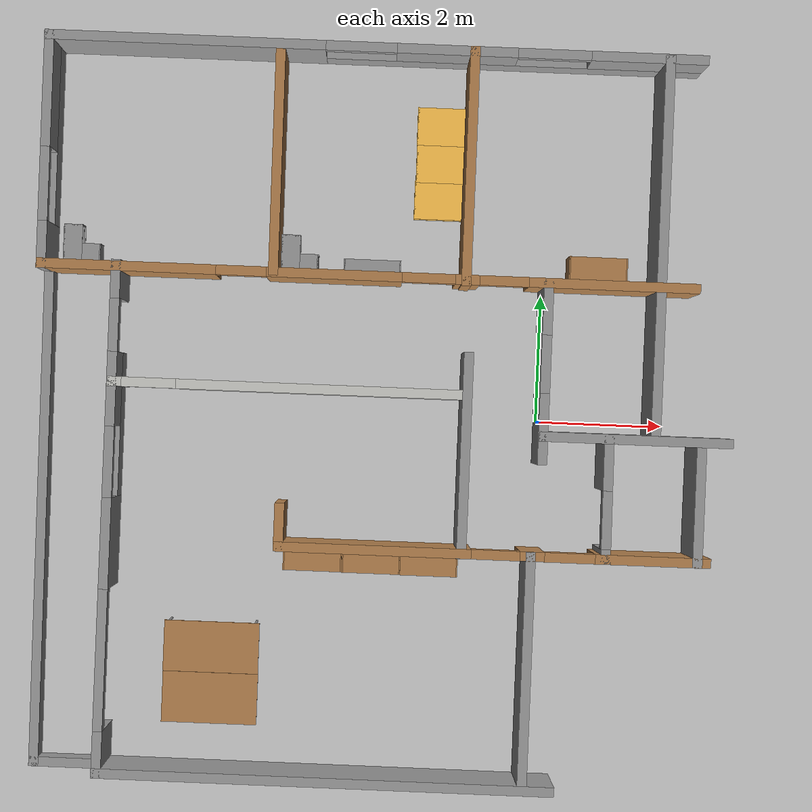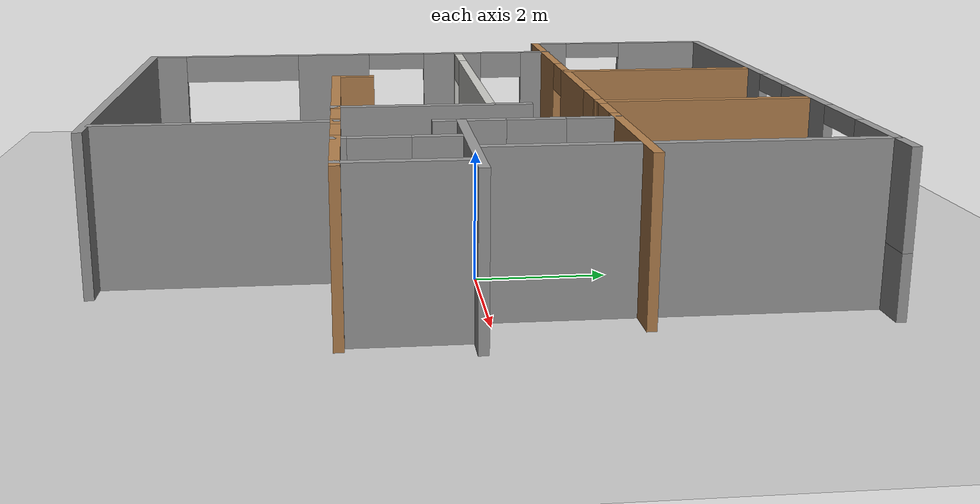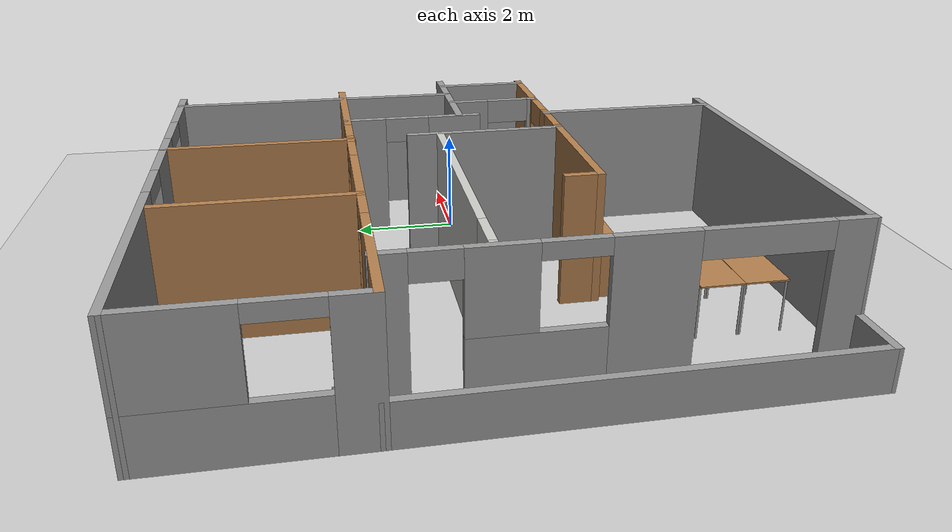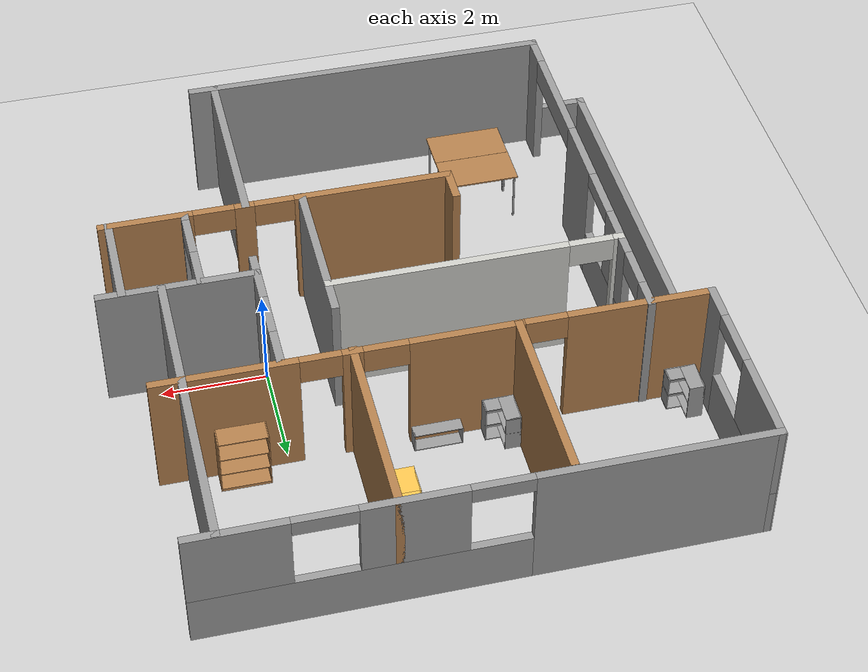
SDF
<sdf version="1.7">
 <world name="default">
  <scene><ambient>0.4 0.4 0.4 1</ambient><background>0.7 0.7 0.7 1</background><shadows>1</shadows></scene>
  <light name="sun" type="directional">
   <pose>0 0 10 0 -0 0</pose>
   <diffuse>0.8 0.8 0.8 1</diffuse>
   <specular>0.2 0.2 0.2 1</specular>
   <attenuation>
    <range>1000</range>
    <constant>0.9</constant>
    <linear>0.01</linear>
    <quadratic>0.001</quadratic>
   </attenuation>
   <direction>-0.5 0.1 -0.9</direction>
   <spot><inner_angle>0</inner_angle><outer_angle>0</outer_angle><falloff>0</falloff></spot>
  </light>
  <model name="ground_plane">
   <static>1</static>
   <link name="link">
    <collision name="collision">
     <geometry><plane><normal>0 0 1</normal><size>100 100</size></plane></geometry>
     <surface><friction><ode><mu>100</mu><mu2>50</mu2></ode></friction></surface>
    </collision>
    <visual name="visual">
     <cast_shadows>0</cast_shadows>
     <geometry><plane><normal>0 0 1</normal><size>100 100</size></plane></geometry>
     <material>
      <script><uri>file://media/materials/scripts/gazebo.material</uri><name>Gazebo/Grey</name></script>
     </material>
    </visual>
   </link>
  </model>
  <physics type="ode">
   <real_time_update_rate>1000</real_time_update_rate>
   <max_step_size>0.001</max_step_size>
   <real_time_factor>1</real_time_factor>
   <ode>
    <solver>
     <type>quick</type>
     <iters>150</iters>
     <precon_iters>0</precon_iters>
     <sor>1.4</sor>
     <use_dynamic_moi_rescaling>1</use_dynamic_moi_rescaling>
    </solver>
    <constraints>
     <cfm>1e-05</cfm>
     <erp>0.2</erp>
     <contact_max_correcting_vel>2000</contact_max_correcting_vel>
     <contact_surface_layer>0.01</contact_surface_layer>
    </constraints>
   </ode>
  </physics>
  <gravity>0 0 -9.8</gravity>
  <magnetic_field>6e-06 2.3e-05 -4.2e-05</magnetic_field>
  <atmosphere type="adiabatic"/>
  <spherical_coordinates>
   <surface_model>EARTH_WGS84</surface_model>
   <latitude_deg>0</latitude_deg>
   <longitude_deg>0</longitude_deg>
   <elevation>0</elevation>
   <heading_deg>0</heading_deg>
  </spherical_coordinates>
  <model name="psr_apartment">
   <pose>-2.46745 -0.010353 0 0 -0 0</pose>
   <link name="Wall_11">
    <pose>-0.304378 5.68028 0 0 -0 0</pose>
    <visual name="Wall_11_Visual_0">
     <pose>-2.95563 0 1.25 0 -0 0</pose>
     <geometry><box><size>4.33874 0.15 2.5</size></box></geometry>
     <material>
      <script><uri>file://media/materials/scripts/gazebo.material</uri><name>Gazebo/Grey</name></script>
      <ambient>1 1 1 1</ambient>
     </material>
     <meta><layer>0</layer></meta>
    </visual>
    <collision name="Wall_11_Collision_0">
     <geometry><box><size>4.33874 0.15 2.5</size></box></geometry>
     <pose>-2.95563 0 1.25 0 -0 0</pose>
    </collision>
    <visual name="Wall_11_Visual_1">
     <pose>2.16937 0 0.5 0 -0 0</pose>
     <geometry><box><size>5.91126 0.15 1</size></box></geometry>
     <material>
      <script><uri>file://media/materials/scripts/gazebo.material</uri><name>Gazebo/Grey</name></script>
      <ambient>1 1 1 1</ambient>
     </material>
     <meta><layer>0</layer></meta>
    </visual>
    <collision name="Wall_11_Collision_1">
     <geometry><box><size>5.91126 0.15 1</size></box></geometry>
     <pose>2.16937 0 0.5 0 -0 0</pose>
    </collision>
    <visual name="Wall_11_Visual_2">
     <pose>1.24874 0 1.75 0 -0 0</pose>
     <geometry><box><size>1.87 0.15 1.5</size></box></geometry>
     <material>
      <script><uri>file://media/materials/scripts/gazebo.material</uri><name>Gazebo/Grey</name></script>
      <ambient>1 1 1 1</ambient>
     </material>
     <meta><layer>0</layer></meta>
    </visual>
    <collision name="Wall_11_Collision_2">
     <geometry><box><size>1.87 0.15 1.5</size></box></geometry>
     <pose>1.24874 0 1.75 0 -0 0</pose>
    </collision>
    <visual name="Wall_11_Visual_3">
     <pose>4.21937 0 1.75 0 -0 0</pose>
     <geometry><box><size>1.81126 0.15 1.5</size></box></geometry>
     <material>
      <script><uri>file://media/materials/scripts/gazebo.material</uri><name>Gazebo/Grey</name></script>
      <ambient>1 1 1 1</ambient>
     </material>
     <meta><layer>0</layer></meta>
    </visual>
    <collision name="Wall_11_Collision_3">
     <geometry><box><size>1.81126 0.15 1.5</size></box></geometry>
     <pose>4.21937 0 1.75 0 -0 0</pose>
    </collision>
    <visual name="Wall_11_Visual_4">
     <pose>-0.236258 0 2.35 0 -0 0</pose>
     <geometry><box><size>1.1 0.15 0.3</size></box></geometry>
     <material>
      <script><uri>file://media/materials/scripts/gazebo.material</uri><name>Gazebo/Grey</name></script>
      <ambient>1 1 1 1</ambient>
     </material>
     <meta><layer>0</layer></meta>
    </visual>
    <collision name="Wall_11_Collision_4">
     <geometry><box><size>1.1 0.15 0.3</size></box></geometry>
     <pose>-0.236258 0 2.35 0 -0 0</pose>
    </collision>
    <visual name="Wall_11_Visual_5">
     <pose>2.74874 0 2.35 0 -0 0</pose>
     <geometry><box><size>1.13 0.15 0.3</size></box></geometry>
     <material>
      <script><uri>file://media/materials/scripts/gazebo.material</uri><name>Gazebo/Grey</name></script>
      <ambient>1 1 1 1</ambient>
     </material>
     <meta><layer>0</layer></meta>
    </visual>
    <collision name="Wall_11_Collision_5">
     <geometry><box><size>1.13 0.15 0.3</size></box></geometry>
     <pose>2.74874 0 2.35 0 -0 0</pose>
    </collision>
   </link>
   <link name="Wall_13">
    <pose>-5.34997 3.91932 0 0 -0 1.5733</pose>
    <visual name="Wall_13_Visual_0">
     <pose>-1.47102 0 1.25 0 -0 0</pose>
     <geometry><box><size>0.73014 0.15 2.5</size></box></geometry>
     <material>
      <script><uri>file://media/materials/scripts/gazebo.material</uri><name>Gazebo/Grey</name></script>
      <ambient>1 1 1 1</ambient>
     </material>
     <meta><layer>0</layer></meta>
    </visual>
    <collision name="Wall_13_Collision_0">
     <geometry><box><size>0.73014 0.15 2.5</size></box></geometry>
     <pose>-1.47102 0 1.25 0 -0 0</pose>
    </collision>
    <visual name="Wall_13_Visual_1">
     <pose>0.36507 0 0.5 0 -0 0</pose>
     <geometry><box><size>2.94204 0.15 1</size></box></geometry>
     <material>
      <script><uri>file://media/materials/scripts/gazebo.material</uri><name>Gazebo/Grey</name></script>
      <ambient>1 1 1 1</ambient>
     </material>
     <meta><layer>0</layer></meta>
    </visual>
    <collision name="Wall_13_Collision_1">
     <geometry><box><size>2.94204 0.15 1</size></box></geometry>
     <pose>0.36507 0 0.5 0 -0 0</pose>
    </collision>
    <visual name="Wall_13_Visual_2">
     <pose>0.93507 0 1.75 0 -0 0</pose>
     <geometry><box><size>1.80204 0.15 1.5</size></box></geometry>
     <material>
      <script><uri>file://media/materials/scripts/gazebo.material</uri><name>Gazebo/Grey</name></script>
      <ambient>1 1 1 1</ambient>
     </material>
     <meta><layer>0</layer></meta>
    </visual>
    <collision name="Wall_13_Collision_2">
     <geometry><box><size>1.80204 0.15 1.5</size></box></geometry>
     <pose>0.93507 0 1.75 0 -0 0</pose>
    </collision>
    <visual name="Wall_13_Visual_3">
     <pose>-0.535949 0 2.35 0 -0 0</pose>
     <geometry><box><size>1.14 0.15 0.3</size></box></geometry>
     <material>
      <script><uri>file://media/materials/scripts/gazebo.material</uri><name>Gazebo/Grey</name></script>
      <ambient>1 1 1 1</ambient>
     </material>
     <meta><layer>0</layer></meta>
    </visual>
    <collision name="Wall_13_Collision_3">
     <geometry><box><size>1.14 0.15 0.3</size></box></geometry>
     <pose>-0.535949 0 2.35 0 -0 0</pose>
    </collision>
   </link>
   <link name="Wall_15">
    <collision name="Wall_15_Collision">
     <geometry><box><size>3.49149 0.15 2.5</size></box></geometry>
     <pose>0 0 1.25 0 -0 0</pose>
    </collision>
    <visual name="Wall_15_Visual">
     <pose>0 0 1.25 0 -0 0</pose>
     <geometry><box><size>3.49149 0.15 2.5</size></box></geometry>
     <material>
      <script><uri>file://media/materials/scripts/gazebo.material</uri><name>Gazebo/Wood</name></script>
      <ambient>1 1 1 1</ambient>
     </material>
     <meta><layer>0</layer></meta>
    </visual>
    <pose>-1.77272 3.85299 0 0 -0 1.57535</pose>
   </link>
   <link name="Wall_17">
    <collision name="Wall_17_Collision">
     <geometry><box><size>3.69364 0.15 2.5</size></box></geometry>
     <pose>0 0 1.25 0 -0 0</pose>
    </collision>
    <visual name="Wall_17_Visual">
     <pose>0 0 1.25 0 -0 0</pose>
     <geometry><box><size>3.69364 0.15 2.5</size></box></geometry>
     <material>
      <script><uri>file://media/materials/scripts/gazebo.material</uri><name>Gazebo/Wood</name></script>
      <ambient>1 1 1 1</ambient>
     </material>
     <meta><layer>0</layer></meta>
    </visual>
    <pose>1.2158 3.90846 0 0 -0 1.5708</pose>
   </link>
   <link name="Wall_19">
    <pose>2.49334 0.790666 0 0 -0 -1.5708</pose>
    <visual name="Wall_19_Visual_0">
     <pose>-1.00243 0 1.25 0 -0 0</pose>
     <geometry><box><size>0.867502 0.15 2.5</size></box></geometry>
     <material>
      <script><uri>file://media/materials/scripts/gazebo.material</uri><name>Gazebo/Grey</name></script>
      <ambient>1 1 1 1</ambient>
     </material>
     <meta><layer>0</layer></meta>
    </visual>
    <collision name="Wall_19_Collision_0">
     <geometry><box><size>0.867502 0.15 2.5</size></box></geometry>
     <pose>-1.00243 0 1.25 0 -0 0</pose>
    </collision>
    <visual name="Wall_19_Visual_1">
     <pose>0.883751 0 1.25 0 -0 0</pose>
     <geometry><box><size>1.10486 0.15 2.5</size></box></geometry>
     <material>
      <script><uri>file://media/materials/scripts/gazebo.material</uri><name>Gazebo/Grey</name></script>
      <ambient>1 1 1 1</ambient>
     </material>
     <meta><layer>0</layer></meta>
    </visual>
    <collision name="Wall_19_Collision_1">
     <geometry><box><size>1.10486 0.15 2.5</size></box></geometry>
     <pose>0.883751 0 1.25 0 -0 0</pose>
    </collision>
    <visual name="Wall_19_Visual_2">
     <pose>-0.118681 0 2.25 0 -0 0</pose>
     <geometry><box><size>0.9 0.15 0.5</size></box></geometry>
     <material>
      <script><uri>file://media/materials/scripts/gazebo.material</uri><name>Gazebo/Grey</name></script>
      <ambient>1 1 1 1</ambient>
     </material>
     <meta><layer>0</layer></meta>
    </visual>
    <collision name="Wall_19_Collision_2">
     <geometry><box><size>0.9 0.15 0.5</size></box></geometry>
     <pose>-0.118681 0 2.25 0 -0 0</pose>
    </collision>
   </link>
   <link name="Wall_2">
    <collision name="Wall_2_Collision">
     <geometry><box><size>7.14201 0.15 2.5</size></box></geometry>
     <pose>0 0 1.25 0 -0 0</pose>
    </collision>
    <visual name="Wall_2_Visual">
     <pose>0 0 1.25 0 -0 0</pose>
     <geometry><box><size>7.14201 0.15 2.5</size></box></geometry>
     <material>
      <script><uri>file://media/materials/scripts/gazebo.material</uri><name>Gazebo/Grey</name></script>
      <ambient>1 1 1 1</ambient>
     </material>
     <meta><layer>0</layer></meta>
    </visual>
    <pose>-0.692508 -5.67455 0 0 -0 -0.00169</pose>
   </link>
   <link name="Wall_21">
    <collision name="Wall_21_Collision">
     <geometry><box><size>3 0.15 2.5</size></box></geometry>
     <pose>0 0 1.25 0 -0 0</pose>
    </collision>
    <visual name="Wall_21_Visual">
     <pose>0 0 1.25 0 -0 0</pose>
     <geometry><box><size>3 0.15 2.5</size></box></geometry>
     <material>
      <script><uri>file://media/materials/scripts/gazebo.material</uri><name>Gazebo/Grey</name></script>
      <ambient>1 1 1 1</ambient>
     </material>
     <meta><layer>0</layer></meta>
    </visual>
    <pose>3.92957 -0.207491 0 0 -0 3.14159</pose>
   </link>
   <link name="Wall_24">
    <pose>1.7781 -2.06515 0 0 -0 0</pose>
    <visual name="Wall_24_Visual_0">
     <pose>-1.84862 0 1.25 0 -0 0</pose>
     <geometry><box><size>3.05276 0.15 2.5</size></box></geometry>
     <material>
      <script><uri>file://media/materials/scripts/gazebo.material</uri><name>Gazebo/Wood</name></script>
      <ambient>1 1 1 1</ambient>
     </material>
     <meta><layer>0</layer></meta>
    </visual>
    <collision name="Wall_24_Collision_0">
     <geometry><box><size>3.05276 0.15 2.5</size></box></geometry>
     <pose>-1.84862 0 1.25 0 -0 0</pose>
    </collision>
    <visual name="Wall_24_Visual_1">
     <pose>0.622094 0 1.25 0 -0 0</pose>
     <geometry><box><size>0.377977 0.15 2.5</size></box></geometry>
     <material>
      <script><uri>file://media/materials/scripts/gazebo.material</uri><name>Gazebo/Wood</name></script>
      <ambient>1 1 1 1</ambient>
     </material>
     <meta><layer>0</layer></meta>
    </visual>
    <collision name="Wall_24_Collision_1">
     <geometry><box><size>0.377977 0.15 2.5</size></box></geometry>
     <pose>0.622094 0 1.25 0 -0 0</pose>
    </collision>
    <visual name="Wall_24_Visual_2">
     <pose>2.48387 0 1.25 0 -0 0</pose>
     <geometry><box><size>1.78227 0.15 2.5</size></box></geometry>
     <material>
      <script><uri>file://media/materials/scripts/gazebo.material</uri><name>Gazebo/Wood</name></script>
      <ambient>1 1 1 1</ambient>
     </material>
     <meta><layer>0</layer></meta>
    </visual>
    <collision name="Wall_24_Collision_2">
     <geometry><box><size>1.78227 0.15 2.5</size></box></geometry>
     <pose>2.48387 0 1.25 0 -0 0</pose>
    </collision>
    <visual name="Wall_24_Visual_3">
     <pose>0.055432 0 2.25 0 -0 0</pose>
     <geometry><box><size>0.755346 0.15 0.5</size></box></geometry>
     <material>
      <script><uri>file://media/materials/scripts/gazebo.material</uri><name>Gazebo/Wood</name></script>
      <ambient>1 1 1 1</ambient>
     </material>
     <meta><layer>0</layer></meta>
    </visual>
    <collision name="Wall_24_Collision_3">
     <geometry><box><size>0.755346 0.15 0.5</size></box></geometry>
     <pose>0.055432 0 2.25 0 -0 0</pose>
    </collision>
    <visual name="Wall_24_Visual_4">
     <pose>1.20191 0 2.25 0 -0 0</pose>
     <geometry><box><size>0.781647 0.15 0.5</size></box></geometry>
     <material>
      <script><uri>file://media/materials/scripts/gazebo.material</uri><name>Gazebo/Wood</name></script>
      <ambient>1 1 1 1</ambient>
     </material>
     <meta><layer>0</layer></meta>
    </visual>
    <collision name="Wall_24_Collision_4">
     <geometry><box><size>0.781647 0.15 0.5</size></box></geometry>
     <pose>1.20191 0 2.25 0 -0 0</pose>
    </collision>
   </link>
   <link name="Wall_27">
    <collision name="Wall_27_Collision">
     <geometry><box><size>2 0.15 2.5</size></box></geometry>
     <pose>0 0 1.25 0 -0 0</pose>
    </collision>
    <visual name="Wall_27_Visual">
     <pose>0 0 1.25 0 -0 0</pose>
     <geometry><box><size>2 0.15 2.5</size></box></geometry>
     <material>
      <script><uri>file://media/materials/scripts/gazebo.material</uri><name>Gazebo/Grey</name></script>
      <ambient>1 1 1 1</ambient>
     </material>
     <meta><layer>0</layer></meta>
    </visual>
    <pose>4.94512 -1.14015 0 0 -0 1.5708</pose>
   </link>
   <link name="Wall_29">
    <pose>3.52344 -1.14601 0 0 -0 -1.5636</pose>
    <visual name="Wall_29_Visual_0">
     <pose>-0.566193 0 1.25 0 -0 0</pose>
     <geometry><box><size>0.855937 0.15 2.5</size></box></geometry>
     <material>
      <script><uri>file://media/materials/scripts/gazebo.material</uri><name>Gazebo/Grey</name></script>
      <ambient>1 1 1 1</ambient>
     </material>
     <meta><layer>0</layer></meta>
    </visual>
    <collision name="Wall_29_Collision_0">
     <geometry><box><size>0.855937 0.15 2.5</size></box></geometry>
     <pose>-0.566193 0 1.25 0 -0 0</pose>
    </collision>
    <visual name="Wall_29_Visual_1">
     <pose>0.877969 0 1.25 0 -0 0</pose>
     <geometry><box><size>0.232385 0.15 2.5</size></box></geometry>
     <material>
      <script><uri>file://media/materials/scripts/gazebo.material</uri><name>Gazebo/Grey</name></script>
      <ambient>1 1 1 1</ambient>
     </material>
     <meta><layer>0</layer></meta>
    </visual>
    <collision name="Wall_29_Collision_1">
     <geometry><box><size>0.232385 0.15 2.5</size></box></geometry>
     <pose>0.877969 0 1.25 0 -0 0</pose>
    </collision>
    <visual name="Wall_29_Visual_2">
     <pose>0.311776 0 2.25 0 -0 0</pose>
     <geometry><box><size>0.9 0.15 0.5</size></box></geometry>
     <material>
      <script><uri>file://media/materials/scripts/gazebo.material</uri><name>Gazebo/Grey</name></script>
      <ambient>1 1 1 1</ambient>
     </material>
     <meta><layer>0</layer></meta>
    </visual>
    <collision name="Wall_29_Collision_2">
     <geometry><box><size>0.9 0.15 0.5</size></box></geometry>
     <pose>0.311776 0 2.25 0 -0 0</pose>
    </collision>
   </link>
   <link name="Wall_31">
    <collision name="Wall_31_Collision">
     <geometry><box><size>3.19175 0.15 2.5</size></box></geometry>
     <pose>0 0 1.25 0 -0 0</pose>
    </collision>
    <visual name="Wall_31_Visual">
     <pose>0 0 1.25 0 -0 0</pose>
     <geometry><box><size>3.19175 0.15 2.5</size></box></geometry>
     <material>
      <script><uri>file://media/materials/scripts/gazebo.material</uri><name>Gazebo/Grey</name></script>
      <ambient>1 1 1 1</ambient>
     </material>
     <meta><layer>0</layer></meta>
    </visual>
    <pose>1.30267 -0.550631 0 0 -0 1.5708</pose>
   </link>
   <link name="Wall_34">
    <pose>-1.44379 0.379575 0 0 -0 0</pose>
    <visual name="Wall_34_Visual_0">
     <pose>-2.70164 0 1.25 0 -0 0</pose>
     <geometry><box><size>0.216714 0.15 2.5</size></box></geometry>
     <material>
      <script><uri>file://media/materials/scripts/gazebo.material</uri><name>Gazebo/CeilingTiled</name></script>
      <ambient>1 1 1 1</ambient>
     </material>
     <meta><layer>0</layer></meta>
    </visual>
    <collision name="Wall_34_Collision_0">
     <geometry><box><size>0.216714 0.15 2.5</size></box></geometry>
     <pose>-2.70164 0 1.25 0 -0 0</pose>
    </collision>
    <visual name="Wall_34_Visual_1">
     <pose>0.528187 0 1.25 0 -0 0</pose>
     <geometry><box><size>4.56363 0.15 2.5</size></box></geometry>
     <material>
      <script><uri>file://media/materials/scripts/gazebo.material</uri><name>Gazebo/CeilingTiled</name></script>
      <ambient>1 1 1 1</ambient>
     </material>
     <meta><layer>0</layer></meta>
    </visual>
    <collision name="Wall_34_Collision_1">
     <geometry><box><size>4.56363 0.15 2.5</size></box></geometry>
     <pose>0.528187 0 1.25 0 -0 0</pose>
    </collision>
    <visual name="Wall_34_Visual_2">
     <pose>-2.17346 0 2.25 0 -0 0</pose>
     <geometry><box><size>0.839659 0.15 0.5</size></box></geometry>
     <material>
      <script><uri>file://media/materials/scripts/gazebo.material</uri><name>Gazebo/CeilingTiled</name></script>
      <ambient>1 1 1 1</ambient>
     </material>
     <meta><layer>0</layer></meta>
    </visual>
    <collision name="Wall_34_Collision_2">
     <geometry><box><size>0.839659 0.15 0.5</size></box></geometry>
     <pose>-2.17346 0 2.25 0 -0 0</pose>
    </collision>
   </link>
   <link name="Wall_36">
    <collision name="Wall_36_Collision">
     <geometry><box><size>0.75 0.15 2.5</size></box></geometry>
     <pose>0 0 1.25 0 -0 0</pose>
    </collision>
    <visual name="Wall_36_Visual">
     <pose>0 0 1.25 0 -0 0</pose>
     <geometry><box><size>0.75 0.15 2.5</size></box></geometry>
     <material>
      <script><uri>file://media/materials/scripts/gazebo.material</uri><name>Gazebo/Wood</name></script>
      <ambient>1 1 1 1</ambient>
     </material>
     <meta><layer>0</layer></meta>
    </visual>
    <pose>-1.5219 -1.76515 0 0 -0 1.5708</pose>
   </link>
   <link name="Wall_39">
    <collision name="Wall_39_Collision">
     <geometry><box><size>3.75 0.15 2.5</size></box></geometry>
     <pose>0 0 1.25 0 -0 0</pose>
    </collision>
    <visual name="Wall_39_Visual">
     <pose>0 0 1.25 0 -0 0</pose>
     <geometry><box><size>3.75 0.15 2.5</size></box></geometry>
     <material>
      <script><uri>file://media/materials/scripts/gazebo.material</uri><name>Gazebo/Grey</name></script>
      <ambient>1 1 1 1</ambient>
     </material>
     <meta><layer>0</layer></meta>
    </visual>
    <pose>2.37648 -3.8696 0 0 -0 -1.5708</pose>
   </link>
   <link name="Wall_4">
    <pose>-4.18851 -1.7438 0 0 -0 1.57079</pose>
    <visual name="Wall_4_Visual_0">
     <pose>-3.64118 0 1.25 0 -0 0</pose>
     <geometry><box><size>0.717646 0.15 2.5</size></box></geometry>
     <material>
      <script><uri>file://media/materials/scripts/gazebo.material</uri><name>Gazebo/Grey</name></script>
      <ambient>1 1 1 1</ambient>
     </material>
     <meta><layer>0</layer></meta>
    </visual>
    <collision name="Wall_4_Collision_0">
     <geometry><box><size>0.717646 0.15 2.5</size></box></geometry>
     <pose>-3.64118 0 1.25 0 -0 0</pose>
    </collision>
    <visual name="Wall_4_Visual_1">
     <pose>-0.38098 0 1.25 0 -0 0</pose>
     <geometry><box><size>1.41075 0.15 2.5</size></box></geometry>
     <material>
      <script><uri>file://media/materials/scripts/gazebo.material</uri><name>Gazebo/Grey</name></script>
      <ambient>1 1 1 1</ambient>
     </material>
     <meta><layer>0</layer></meta>
    </visual>
    <collision name="Wall_4_Collision_1">
     <geometry><box><size>1.41075 0.15 2.5</size></box></geometry>
     <pose>-0.38098 0 1.25 0 -0 0</pose>
    </collision>
    <visual name="Wall_4_Visual_2">
     <pose>3.70228 0 1.25 0 -0 0</pose>
     <geometry><box><size>0.59543 0.15 2.5</size></box></geometry>
     <material>
      <script><uri>file://media/materials/scripts/gazebo.material</uri><name>Gazebo/Grey</name></script>
      <ambient>1 1 1 1</ambient>
     </material>
     <meta><layer>0</layer></meta>
    </visual>
    <collision name="Wall_4_Collision_2">
     <geometry><box><size>0.59543 0.15 2.5</size></box></geometry>
     <pose>3.70228 0 1.25 0 -0 0</pose>
    </collision>
    <visual name="Wall_4_Visual_3">
     <pose>1.45361 0 0.5 0 -0 0</pose>
     <geometry><box><size>2.25844 0.15 1</size></box></geometry>
     <material>
      <script><uri>file://media/materials/scripts/gazebo.material</uri><name>Gazebo/Grey</name></script>
      <ambient>1 1 1 1</ambient>
     </material>
     <meta><layer>0</layer></meta>
    </visual>
    <collision name="Wall_4_Collision_3">
     <geometry><box><size>2.25844 0.15 1</size></box></geometry>
     <pose>1.45361 0 0.5 0 -0 0</pose>
    </collision>
    <visual name="Wall_4_Visual_4">
     <pose>2.00561 0 1.75 0 -0 0</pose>
     <geometry><box><size>1.15444 0.15 1.5</size></box></geometry>
     <material>
      <script><uri>file://media/materials/scripts/gazebo.material</uri><name>Gazebo/Grey</name></script>
      <ambient>1 1 1 1</ambient>
     </material>
     <meta><layer>0</layer></meta>
    </visual>
    <collision name="Wall_4_Collision_4">
     <geometry><box><size>1.15444 0.15 1.5</size></box></geometry>
     <pose>2.00561 0 1.75 0 -0 0</pose>
    </collision>
    <visual name="Wall_4_Visual_5">
     <pose>-2.18435 0 2.25 0 -0 0</pose>
     <geometry><box><size>2.196 0.15 0.5</size></box></geometry>
     <material>
      <script><uri>file://media/materials/scripts/gazebo.material</uri><name>Gazebo/Grey</name></script>
      <ambient>1 1 1 1</ambient>
     </material>
     <meta><layer>0</layer></meta>
    </visual>
    <collision name="Wall_4_Collision_5">
     <geometry><box><size>2.196 0.15 0.5</size></box></geometry>
     <pose>-2.18435 0 2.25 0 -0 0</pose>
    </collision>
    <visual name="Wall_4_Visual_6">
     <pose>2.9937 0 2.25 0 -0 0</pose>
     <geometry><box><size>0.821739 0.15 0.5</size></box></geometry>
     <material>
      <script><uri>file://media/materials/scripts/gazebo.material</uri><name>Gazebo/Grey</name></script>
      <ambient>1 1 1 1</ambient>
     </material>
     <meta><layer>0</layer></meta>
    </visual>
    <collision name="Wall_4_Collision_6">
     <geometry><box><size>0.821739 0.15 0.5</size></box></geometry>
     <pose>2.9937 0 2.25 0 -0 0</pose>
    </collision>
    <visual name="Wall_4_Visual_7">
     <pose>0.876393 0 2.35 0 -0 0</pose>
     <geometry><box><size>1.104 0.15 0.3</size></box></geometry>
     <material>
      <script><uri>file://media/materials/scripts/gazebo.material</uri><name>Gazebo/Grey</name></script>
      <ambient>1 1 1 1</ambient>
     </material>
     <meta><layer>0</layer></meta>
    </visual>
    <collision name="Wall_4_Collision_7">
     <geometry><box><size>1.104 0.15 0.3</size></box></geometry>
     <pose>0.876393 0 2.35 0 -0 0</pose>
    </collision>
   </link>
   <link name="Wall_41">
    <collision name="Wall_41_Collision">
     <geometry><box><size>1.25 0.15 0.8</size></box></geometry>
     <pose>0 0 0.4 0 -0 0</pose>
    </collision>
    <visual name="Wall_41_Visual">
     <pose>0 0 0.4 0 -0 0</pose>
     <geometry><box><size>1.25 0.15 0.8</size></box></geometry>
     <material>
      <script><uri>file://media/materials/scripts/gazebo.material</uri><name>Gazebo/Grey</name></script>
      <ambient>0.368627 0.384314 0.352941 1</ambient>
     </material>
     <meta><layer>0</layer></meta>
    </visual>
    <pose>-4.73855 -5.66865 0 0 -0 3.14159</pose>
   </link>
   <link name="Wall_42">
    <collision name="Wall_42_Collision">
     <geometry><box><size>7.97728 0.15 0.8</size></box></geometry>
     <pose>0 0 0.4 0 -0 0</pose>
    </collision>
    <visual name="Wall_42_Visual">
     <pose>0 0 0.4 0 -0 0</pose>
     <geometry><box><size>7.97728 0.15 0.8</size></box></geometry>
     <material>
      <script><uri>file://media/materials/scripts/gazebo.material</uri><name>Gazebo/Grey</name></script>
      <ambient>0.368627 0.384314 0.352941 1</ambient>
     </material>
     <meta><layer>0</layer></meta>
    </visual>
    <pose>-5.31705 -1.75515 0 0 -0 1.57808</pose>
   </link>
   <link name="Wall_6">
    <pose>-0.295353 2.15823 0 0 -0 -2.4e-05</pose>
    <visual name="Wall_6_Visual_0">
     <pose>-3.73944 0 1.25 0 -0 0</pose>
     <geometry><box><size>2.77111 0.15 2.5</size></box></geometry>
     <material>
      <script><uri>file://media/materials/scripts/gazebo.material</uri><name>Gazebo/Wood</name></script>
      <ambient>1 1 1 1</ambient>
     </material>
     <meta><layer>0</layer></meta>
    </visual>
    <collision name="Wall_6_Collision_0">
     <geometry><box><size>2.77111 0.15 2.5</size></box></geometry>
     <pose>-3.73944 0 1.25 0 -0 0</pose>
    </collision>
    <visual name="Wall_6_Visual_1">
     <pose>-0.52611 0 1.25 0 -0 0</pose>
     <geometry><box><size>2.09692 0.15 2.5</size></box></geometry>
     <material>
      <script><uri>file://media/materials/scripts/gazebo.material</uri><name>Gazebo/Wood</name></script>
      <ambient>1 1 1 1</ambient>
     </material>
     <meta><layer>0</layer></meta>
    </visual>
    <collision name="Wall_6_Collision_1">
     <geometry><box><size>2.09692 0.15 2.5</size></box></geometry>
     <pose>-0.52611 0 1.25 0 -0 0</pose>
    </collision>
    <visual name="Wall_6_Visual_2">
     <pose>1.53051 0 1.25 0 -0 0</pose>
     <geometry><box><size>0.377215 0.15 2.5</size></box></geometry>
     <material>
      <script><uri>file://media/materials/scripts/gazebo.material</uri><name>Gazebo/Wood</name></script>
      <ambient>1 1 1 1</ambient>
     </material>
     <meta><layer>0</layer></meta>
    </visual>
    <collision name="Wall_6_Collision_2">
     <geometry><box><size>0.377215 0.15 2.5</size></box></geometry>
     <pose>1.53051 0 1.25 0 -0 0</pose>
    </collision>
    <visual name="Wall_6_Visual_3">
     <pose>3.80166 0 1.25 0 -0 0</pose>
     <geometry><box><size>2.64668 0.15 2.5</size></box></geometry>
     <material>
      <script><uri>file://media/materials/scripts/gazebo.material</uri><name>Gazebo/Wood</name></script>
      <ambient>1 1 1 1</ambient>
     </material>
     <meta><layer>0</layer></meta>
    </visual>
    <collision name="Wall_6_Collision_3">
     <geometry><box><size>2.64668 0.15 2.5</size></box></geometry>
     <pose>3.80166 0 1.25 0 -0 0</pose>
    </collision>
    <visual name="Wall_6_Visual_4">
     <pose>-1.96423 0 2.25 0 -0 0</pose>
     <geometry><box><size>0.779319 0.15 0.5</size></box></geometry>
     <material>
      <script><uri>file://media/materials/scripts/gazebo.material</uri><name>Gazebo/Wood</name></script>
      <ambient>1 1 1 1</ambient>
     </material>
     <meta><layer>0</layer></meta>
    </visual>
    <collision name="Wall_6_Collision_4">
     <geometry><box><size>0.779319 0.15 0.5</size></box></geometry>
     <pose>-1.96423 0 2.25 0 -0 0</pose>
    </collision>
    <visual name="Wall_6_Visual_5">
     <pose>0.932124 0 2.25 0 -0 0</pose>
     <geometry><box><size>0.819546 0.15 0.5</size></box></geometry>
     <material>
      <script><uri>file://media/materials/scripts/gazebo.material</uri><name>Gazebo/Wood</name></script>
      <ambient>1 1 1 1</ambient>
     </material>
     <meta><layer>0</layer></meta>
    </visual>
    <collision name="Wall_6_Collision_5">
     <geometry><box><size>0.819546 0.15 0.5</size></box></geometry>
     <pose>0.932124 0 2.25 0 -0 0</pose>
    </collision>
    <visual name="Wall_6_Visual_6">
     <pose>2.09872 0 2.25 0 -0 0</pose>
     <geometry><box><size>0.759206 0.15 0.5</size></box></geometry>
     <material>
      <script><uri>file://media/materials/scripts/gazebo.material</uri><name>Gazebo/Wood</name></script>
      <ambient>1 1 1 1</ambient>
     </material>
     <meta><layer>0</layer></meta>
    </visual>
    <collision name="Wall_6_Collision_6">
     <geometry><box><size>0.759206 0.15 0.5</size></box></geometry>
     <pose>2.09872 0 2.25 0 -0 0</pose>
    </collision>
   </link>
   <link name="Wall_9">
    <collision name="Wall_9_Collision">
     <geometry><box><size>6 0.15 2.5</size></box></geometry>
     <pose>0 0 1.25 0 -0 0</pose>
    </collision>
    <visual name="Wall_9_Visual">
     <pose>0 0 1.25 0 -0 0</pose>
     <geometry><box><size>6 0.15 2.5</size></box></geometry>
     <material>
      <script><uri>file://media/materials/scripts/gazebo.material</uri><name>Gazebo/Grey</name></script>
      <ambient>1 1 1 1</ambient>
     </material>
     <meta><layer>0</layer></meta>
    </visual>
    <pose>4.22713 2.74007 0 0 -0 -1.5708</pose>
   </link>
   <static>1</static>
  </model>
  <model name="Wall_Cabinet_36x15W">
   <link name="Wall_0">
    <pose>0 0 0.01 0 -0 0</pose>
    <inertial>
     <mass>1.9796</mass>
     <inertia><ixx>0.0145</ixx><iyy>0.1511</iyy><izz>0.1367</izz><ixy>0</ixy><ixz>0</ixz><iyz>0</iyz></inertia>
    </inertial>
    <collision name="Wall_0_Collision"><geometry><box><size>0.91 0.296 0.02</size></box></geometry></collision>
    <visual name="Wall_0_Visual">
     <geometry><box><size>0.91 0.296 0.02</size></box></geometry>
     <material>
      <script><uri>file://media/materials/scripts/gazebo.material</uri><name>Gazebo/Grey</name></script>
      <ambient>1 1 1 1</ambient>
     </material>
    </visual>
   </link>
   <joint name="0_2" type="fixed">
    <pose>-0.455 0 0 0 -0 0</pose>
    <parent>Wall_2</parent>
    <child>Wall_0</child>
    <axis><xyz>0 0 1</xyz><limit><lower>-1e+16</lower><upper>1e+16</upper></limit></axis>
   </joint>
   <joint name="0_4" type="fixed">
    <pose>0.455 0 0 0 -0 0</pose>
    <parent>Wall_4</parent>
    <child>Wall_0</child>
    <axis><xyz>0 0 1</xyz><limit><lower>-1e+16</lower><upper>1e+16</upper></limit></axis>
   </joint>
   <joint name="0_8" type="fixed">
    <pose>0 -0.148 0 0 -0 0</pose>
    <parent>Wall_8</parent>
    <child>Wall_0</child>
    <axis><xyz>0 0 1</xyz><limit><lower>-1e+16</lower><upper>1e+16</upper></limit></axis>
   </joint>
   <link name="Wall_2">
    <pose>-0.445 0 0.192 0 -0 0</pose>
    <inertial>
     <mass>0.8353</mass>
     <inertia><ixx>0.0061</ixx><iyy>0.0164</iyy><izz>0.0103</izz><ixy>0</ixy><ixz>0</ixz><iyz>0</iyz></inertia>
    </inertial>
    <collision name="Wall_2_Collision"><geometry><box><size>0.02 0.296 0.384</size></box></geometry></collision>
    <visual name="Wall_2_Visual">
     <geometry><box><size>0.02 0.296 0.384</size></box></geometry>
     <material>
      <script><uri>file://media/materials/scripts/gazebo.material</uri><name>Gazebo/Grey</name></script>
      <ambient>1 1 1 1</ambient>
     </material>
    </visual>
   </link>
   <link name="Wall_4">
    <pose>0.445 0 0.192 0 -0 0</pose>
    <inertial>
     <mass>0.8353</mass>
     <inertia><ixx>0.0061</ixx><iyy>0.0164</iyy><izz>0.0103</izz><ixy>0</ixy><ixz>0</ixz><iyz>0</iyz></inertia>
    </inertial>
    <collision name="Wall_4_Collision"><geometry><box><size>0.02 0.296 0.384</size></box></geometry></collision>
    <visual name="Wall_4_Visual">
     <geometry><box><size>0.02 0.296 0.384</size></box></geometry>
     <material>
      <script><uri>file://media/materials/scripts/gazebo.material</uri><name>Gazebo/Grey</name></script>
      <ambient>1 1 1 1</ambient>
     </material>
    </visual>
   </link>
   <link name="Wall_6">
    <pose>0 0 0.374 0 -0 0</pose>
    <inertial>
     <mass>1.9796</mass>
     <inertia><ixx>0.0145</ixx><iyy>0.1511</iyy><izz>0.1367</izz><ixy>0</ixy><ixz>0</ixz><iyz>0</iyz></inertia>
    </inertial>
    <collision name="Wall_6_Collision"><geometry><box><size>0.91 0.296 0.02</size></box></geometry></collision>
    <visual name="Wall_6_Visual">
     <geometry><box><size>0.91 0.296 0.02</size></box></geometry>
     <material>
      <script><uri>file://media/materials/scripts/gazebo.material</uri><name>Gazebo/Grey</name></script>
      <ambient>1 1 1 1</ambient>
     </material>
    </visual>
   </link>
   <joint name="6_2" type="fixed">
    <pose>-0.455 0 0 0 -0 0</pose>
    <parent>Wall_2</parent>
    <child>Wall_6</child>
    <axis><xyz>0 0 1</xyz><limit><lower>-1e+16</lower><upper>1e+16</upper></limit></axis>
   </joint>
   <joint name="6_4" type="fixed">
    <pose>0.455 0 0 0 -0 0</pose>
    <parent>Wall_4</parent>
    <child>Wall_6</child>
    <axis><xyz>0 0 1</xyz><limit><lower>-1e+16</lower><upper>1e+16</upper></limit></axis>
   </joint>
   <joint name="6_8" type="fixed">
    <pose>0 -0.148 0 0 -0 0</pose>
    <parent>Wall_8</parent>
    <child>Wall_6</child>
    <axis><xyz>0 0 1</xyz><limit><lower>-1e+16</lower><upper>1e+16</upper></limit></axis>
   </joint>
   <link name="Wall_8">
    <pose>0 -0.138 0.19 0 -0 0</pose>
    <inertial>
     <mass>2.5302</mass>
     <inertia><ixx>0.0305</ixx><iyy>0.1732</iyy><izz>0.2035</izz><ixy>0</ixy><ixz>0</ixz><iyz>0</iyz></inertia>
    </inertial>
    <collision name="Wall_8_Collision"><geometry><box><size>0.906 0.02 0.38</size></box></geometry></collision>
    <visual name="Wall_8_Visual">
     <geometry><box><size>0.906 0.02 0.38</size></box></geometry>
     <material>
      <script><uri>file://media/materials/scripts/gazebo.material</uri><name>Gazebo/Grey</name></script>
      <ambient>1 1 1 1</ambient>
     </material>
    </visual>
   </link>
   <joint name="8_2" type="fixed">
    <pose>-0.453 0 0 0 -0 0</pose>
    <parent>Wall_2</parent>
    <child>Wall_8</child>
    <axis><xyz>0 1 0</xyz><limit><lower>-1e+16</lower><upper>1e+16</upper></limit></axis>
   </joint>
   <joint name="8_4" type="fixed">
    <pose>0.453 0 0 0 -0 0</pose>
    <parent>Wall_4</parent>
    <child>Wall_8</child>
    <axis><xyz>0 1 0</xyz><limit><lower>-1e+16</lower><upper>1e+16</upper></limit></axis>
   </joint>
   <static>1</static>
   <pose>-2.71246 2.32688 0 0 -0 0</pose>
  </model>
  <model name="Wall_Cabinet_Coin_24x30W">
   <link name="Wall_10">
    <pose>0.286 -0.148 0.384 0 -0 0</pose>
    <inertial>
     <mass>2.1259</mass>
     <inertia><ixx>0.0158</ixx><iyy>0.1202</iyy><izz>0.1046</izz><ixy>0</ixy><ixz>0</ixz><iyz>0</iyz></inertia>
    </inertial>
    <collision name="Wall_10_Collision"><geometry><box><size>0.02 0.296 0.768</size></box></geometry></collision>
    <visual name="Wall_10_Visual">
     <geometry><box><size>0.02 0.296 0.768</size></box></geometry>
     <material>
      <script><uri>file://media/materials/scripts/gazebo.material</uri><name>Gazebo/Grey</name></script>
      <ambient>1 1 1 1</ambient>
     </material>
    </visual>
   </link>
   <joint name="10_16" type="fixed">
    <pose>0 0 -0.374 0 -0 0</pose>
    <parent>Wall_16</parent>
    <child>Wall_10</child>
    <axis><xyz>1 0 0</xyz><limit><lower>-1e+16</lower><upper>1e+16</upper></limit></axis>
   </joint>
   <joint name="10_14" type="fixed">
    <parent>Wall_14</parent>
    <child>Wall_10</child>
    <axis><xyz>1 0 0</xyz><limit><lower>-1e+16</lower><upper>1e+16</upper></limit></axis>
   </joint>
   <joint name="10_12" type="fixed">
    <pose>0 0 0.374 0 -0 0</pose>
    <parent>Wall_12</parent>
    <child>Wall_10</child>
    <axis><xyz>1 0 0</xyz><limit><lower>-1e+16</lower><upper>1e+16</upper></limit></axis>
   </joint>
   <joint name="10_29" type="fixed">
    <pose>0 -0.148 0 0 -0 0</pose>
    <parent>Wall_29</parent>
    <child>Wall_10</child>
    <axis><xyz>1 0 0</xyz><limit><lower>-1e+16</lower><upper>1e+16</upper></limit></axis>
   </joint>
   <link name="Wall_12">
    <pose>0.148 -0.148 0.758 0 -0 0</pose>
    <inertial>
     <mass>0.8802</mass>
     <inertia><ixx>0.0065</ixx><iyy>0.0139</iyy><izz>0.0074</izz><ixy>0</ixy><ixz>0</ixz><iyz>0</iyz></inertia>
    </inertial>
    <collision name="Wall_12_Collision"><geometry><box><size>0.296 0.296 0.02</size></box></geometry></collision>
    <visual name="Wall_12_Visual">
     <geometry><box><size>0.296 0.296 0.02</size></box></geometry>
     <material>
      <script><uri>file://media/materials/scripts/gazebo.material</uri><name>Gazebo/Grey</name></script>
      <ambient>1 1 1 1</ambient>
     </material>
    </visual>
   </link>
   <joint name="12_29" type="fixed">
    <pose>0 -0.148 0 0 -0 0</pose>
    <parent>Wall_29</parent>
    <child>Wall_12</child>
    <axis><xyz>0 0 1</xyz><limit><lower>-1e+16</lower><upper>1e+16</upper></limit></axis>
   </joint>
   <link name="Wall_14">
    <pose>0.148 -0.148 0.384 0 -0 0</pose>
    <inertial>
     <mass>0.8802</mass>
     <inertia><ixx>0.0065</ixx><iyy>0.0139</iyy><izz>0.0074</izz><ixy>0</ixy><ixz>0</ixz><iyz>0</iyz></inertia>
    </inertial>
    <collision name="Wall_14_Collision"><geometry><box><size>0.296 0.296 0.02</size></box></geometry></collision>
    <visual name="Wall_14_Visual">
     <geometry><box><size>0.296 0.296 0.02</size></box></geometry>
     <material>
      <script><uri>file://media/materials/scripts/gazebo.material</uri><name>Gazebo/Grey</name></script>
      <ambient>1 1 1 1</ambient>
     </material>
    </visual>
   </link>
   <joint name="14_29" type="fixed">
    <pose>0 -0.148 0 0 -0 0</pose>
    <parent>Wall_29</parent>
    <child>Wall_14</child>
    <axis><xyz>0 1 0</xyz><limit><lower>-1e+16</lower><upper>1e+16</upper></limit></axis>
   </joint>
   <link name="Wall_16">
    <pose>0.148 -0.148 0.01 0 -0 0</pose>
    <inertial>
     <mass>0.8802</mass>
     <inertia><ixx>0.0065</ixx><iyy>0.0139</iyy><izz>0.0074</izz><ixy>0</ixy><ixz>0</ixz><iyz>0</iyz></inertia>
    </inertial>
    <collision name="Wall_16_Collision"><geometry><box><size>0.296 0.296 0.02</size></box></geometry></collision>
    <visual name="Wall_16_Visual">
     <geometry><box><size>0.296 0.296 0.02</size></box></geometry>
     <material>
      <script><uri>file://media/materials/scripts/gazebo.material</uri><name>Gazebo/Grey</name></script>
      <ambient>1 1 1 1</ambient>
     </material>
    </visual>
   </link>
   <joint name="16_29" type="fixed">
    <pose>0 -0.148 0 0 -0 0</pose>
    <parent>Wall_29</parent>
    <child>Wall_16</child>
    <axis><xyz>0 1 0</xyz><limit><lower>-1e+16</lower><upper>1e+16</upper></limit></axis>
   </joint>
   <link name="Wall_18">
    <pose>-0.148 0 0.01 0 -0 0</pose>
    <inertial>
     <mass>1.6525</mass>
     <inertia><ixx>0.0491</ixx><iyy>0.0613</iyy><izz>0.0123</izz><ixy>0</ixy><ixz>0</ixz><iyz>0</iyz></inertia>
    </inertial>
    <collision name="Wall_18_Collision"><geometry><box><size>0.296 0.592 0.02</size></box></geometry></collision>
    <visual name="Wall_18_Visual">
     <geometry><box><size>0.296 0.592 0.02</size></box></geometry>
     <material>
      <script><uri>file://media/materials/scripts/gazebo.material</uri><name>Gazebo/Grey</name></script>
      <ambient>1 1 1 1</ambient>
     </material>
    </visual>
   </link>
   <joint name="18_16" type="fixed">
    <pose>0.148 -0.148 0 0 -0 0</pose>
    <parent>Wall_16</parent>
    <child>Wall_18</child>
    <axis><xyz>1 0 0</xyz><limit><lower>-1e+16</lower><upper>1e+16</upper></limit></axis>
   </joint>
   <joint name="18_29" type="fixed">
    <pose>0 -0.296 0 0 -0 0</pose>
    <parent>Wall_29</parent>
    <child>Wall_18</child>
    <axis><xyz>0 1 0</xyz><limit><lower>-1e+16</lower><upper>1e+16</upper></limit></axis>
   </joint>
   <joint name="18_27" type="fixed">
    <pose>-0.148 0 0 0 -0 0</pose>
    <parent>Wall_27</parent>
    <child>Wall_18</child>
    <axis><xyz>1 0 0</xyz><limit><lower>-1e+16</lower><upper>1e+16</upper></limit></axis>
   </joint>
   <joint name="18_30" type="fixed">
    <pose>0 0.296 0 0 -0 0</pose>
    <parent>Wall_30</parent>
    <child>Wall_18</child>
    <axis><xyz>0 1 0</xyz><limit><lower>-1e+16</lower><upper>1e+16</upper></limit></axis>
   </joint>
   <link name="Wall_20">
    <pose>-0.148 0 0.384 0 -0 0</pose>
    <inertial>
     <mass>1.6525</mass>
     <inertia><ixx>0.0491</ixx><iyy>0.0613</iyy><izz>0.0123</izz><ixy>0</ixy><ixz>0</ixz><iyz>0</iyz></inertia>
    </inertial>
    <collision name="Wall_20_Collision"><geometry><box><size>0.296 0.592 0.02</size></box></geometry></collision>
    <visual name="Wall_20_Visual">
     <geometry><box><size>0.296 0.592 0.02</size></box></geometry>
     <material>
      <script><uri>file://media/materials/scripts/gazebo.material</uri><name>Gazebo/Grey</name></script>
      <ambient>1 1 1 1</ambient>
     </material>
    </visual>
   </link>
   <joint name="20_14" type="fixed">
    <pose>0.148 -0.148 0 0 -0 0</pose>
    <parent>Wall_14</parent>
    <child>Wall_20</child>
    <axis><xyz>1 0 0</xyz><limit><lower>-1e+16</lower><upper>1e+16</upper></limit></axis>
   </joint>
   <joint name="20_29" type="fixed">
    <pose>0 -0.296 0 0 -0 0</pose>
    <parent>Wall_29</parent>
    <child>Wall_20</child>
    <axis><xyz>0 1 0</xyz><limit><lower>-1e+16</lower><upper>1e+16</upper></limit></axis>
   </joint>
   <joint name="20_27" type="fixed">
    <pose>-0.148 0 0 0 -0 0</pose>
    <parent>Wall_27</parent>
    <child>Wall_20</child>
    <axis><xyz>1 0 0</xyz><limit><lower>-1e+16</lower><upper>1e+16</upper></limit></axis>
   </joint>
   <joint name="20_30" type="fixed">
    <pose>0 0.296 0 0 -0 0</pose>
    <parent>Wall_30</parent>
    <child>Wall_20</child>
    <axis><xyz>0 1 0</xyz><limit><lower>-1e+16</lower><upper>1e+16</upper></limit></axis>
   </joint>
   <link name="Wall_22">
    <pose>-0.148 0 0.758 0 -0 0</pose>
    <inertial>
     <mass>1.6525</mass>
     <inertia><ixx>0.0491</ixx><iyy>0.0613</iyy><izz>0.0123</izz><ixy>0</ixy><ixz>0</ixz><iyz>0</iyz></inertia>
    </inertial>
    <collision name="Wall_22_Collision"><geometry><box><size>0.296 0.592 0.02</size></box></geometry></collision>
    <visual name="Wall_22_Visual">
     <geometry><box><size>0.296 0.592 0.02</size></box></geometry>
     <material>
      <script><uri>file://media/materials/scripts/gazebo.material</uri><name>Gazebo/Grey</name></script>
      <ambient>1 1 1 1</ambient>
     </material>
    </visual>
   </link>
   <joint name="22_12" type="fixed">
    <pose>0.148 -0.148 0 0 -0 0</pose>
    <parent>Wall_12</parent>
    <child>Wall_22</child>
    <axis><xyz>1 0 0</xyz><limit><lower>-1e+16</lower><upper>1e+16</upper></limit></axis>
   </joint>
   <joint name="22_29" type="fixed">
    <pose>0 -0.296 0 0 -0 0</pose>
    <parent>Wall_29</parent>
    <child>Wall_22</child>
    <axis><xyz>0 1 0</xyz><limit><lower>-1e+16</lower><upper>1e+16</upper></limit></axis>
   </joint>
   <joint name="22_27" type="fixed">
    <pose>-0.148 0 0 0 -0 0</pose>
    <parent>Wall_27</parent>
    <child>Wall_22</child>
    <axis><xyz>1 0 0</xyz><limit><lower>-1e+16</lower><upper>1e+16</upper></limit></axis>
   </joint>
   <joint name="22_30" type="fixed">
    <pose>0 0.296 0 0 -0 0</pose>
    <parent>Wall_30</parent>
    <child>Wall_22</child>
    <axis><xyz>0 1 0</xyz><limit><lower>-1e+16</lower><upper>1e+16</upper></limit></axis>
   </joint>
   <link name="Wall_27">
    <pose>-0.286 0 0.384 0 -0 0</pose>
    <inertial>
     <mass>4.2589</mass>
     <inertia><ixx>0.1266</ixx><iyy>0.3358</iyy><izz>0.2095</izz><ixy>0</ixy><ixz>0</ixz><iyz>0</iyz></inertia>
    </inertial>
    <collision name="Wall_27_Collision"><geometry><box><size>0.02 0.592 0.768</size></box></geometry></collision>
    <visual name="Wall_27_Visual">
     <geometry><box><size>0.02 0.592 0.768</size></box></geometry>
     <material>
      <script><uri>file://media/materials/scripts/gazebo.material</uri><name>Gazebo/Grey</name></script>
      <ambient>1 1 1 1</ambient>
     </material>
    </visual>
   </link>
   <joint name="27_30" type="fixed">
    <pose>0 0.296 0 0 -0 0</pose>
    <parent>Wall_30</parent>
    <child>Wall_27</child>
    <axis><xyz>0 1 0</xyz><limit><lower>-1e+16</lower><upper>1e+16</upper></limit></axis>
   </joint>
   <link name="Wall_29">
    <pose>0 -0.286 0.384 0 -0 0</pose>
    <inertial>
     <mass>4.3176</mass>
     <inertia><ixx>0.134</ixx><iyy>0.2091</iyy><izz>0.3428</izz><ixy>0</ixy><ixz>0</ixz><iyz>0</iyz></inertia>
    </inertial>
    <collision name="Wall_29_Collision"><geometry><box><size>0.592 0.02 0.768</size></box></geometry></collision>
    <visual name="Wall_29_Visual">
     <geometry><box><size>0.592 0.02 0.768</size></box></geometry>
     <material>
      <script><uri>file://media/materials/scripts/gazebo.material</uri><name>Gazebo/Grey</name></script>
      <ambient>1 1 1 1</ambient>
     </material>
    </visual>
   </link>
   <link name="Wall_30">
    <pose>-0.148 0.286 0.384 0 -0 0</pose>
    <inertial>
     <mass>2.1093</mass>
     <inertia><ixx>0.1021</ixx><iyy>0.0157</iyy><izz>0.1177</izz><ixy>0</ixy><ixz>0</ixz><iyz>0</iyz></inertia>
    </inertial>
    <collision name="Wall_30_Collision"><geometry><box><size>0.296 0.02 0.768</size></box></geometry></collision>
    <visual name="Wall_30_Visual">
     <geometry><box><size>0.296 0.02 0.768</size></box></geometry>
     <material>
      <script><uri>file://media/materials/scripts/gazebo.material</uri><name>Gazebo/Grey</name></script>
      <ambient>1 1 1 1</ambient>
     </material>
    </visual>
   </link>
   <static>1</static>
   <pose>-3.86335 2.51029 0 0 -0 0</pose>
  </model>
  <model name="Wall_Cabinet_Coin_24x30W_clone">
   <link name="Wall_10">
    <pose>0.286 -0.148 0.384 0 -0 0</pose>
    <inertial>
     <mass>2.1259</mass>
     <inertia><ixx>0.0158</ixx><iyy>0.1202</iyy><izz>0.1046</izz><ixy>0</ixy><ixz>0</ixz><iyz>0</iyz></inertia>
    </inertial>
    <collision name="Wall_10_Collision"><geometry><box><size>0.02 0.296 0.768</size></box></geometry></collision>
    <visual name="Wall_10_Visual">
     <geometry><box><size>0.02 0.296 0.768</size></box></geometry>
     <material>
      <script><uri>file://media/materials/scripts/gazebo.material</uri><name>Gazebo/Grey</name></script>
      <ambient>1 1 1 1</ambient>
     </material>
    </visual>
   </link>
   <joint name="10_16" type="fixed">
    <pose>0 0 -0.374 0 -0 0</pose>
    <parent>Wall_16</parent>
    <child>Wall_10</child>
    <axis><xyz>1 0 0</xyz><limit><lower>-1e+16</lower><upper>1e+16</upper></limit></axis>
   </joint>
   <joint name="10_14" type="fixed">
    <parent>Wall_14</parent>
    <child>Wall_10</child>
    <axis><xyz>1 0 0</xyz><limit><lower>-1e+16</lower><upper>1e+16</upper></limit></axis>
   </joint>
   <joint name="10_12" type="fixed">
    <pose>0 0 0.374 0 -0 0</pose>
    <parent>Wall_12</parent>
    <child>Wall_10</child>
    <axis><xyz>1 0 0</xyz><limit><lower>-1e+16</lower><upper>1e+16</upper></limit></axis>
   </joint>
   <joint name="10_29" type="fixed">
    <pose>0 -0.148 0 0 -0 0</pose>
    <parent>Wall_29</parent>
    <child>Wall_10</child>
    <axis><xyz>1 0 0</xyz><limit><lower>-1e+16</lower><upper>1e+16</upper></limit></axis>
   </joint>
   <link name="Wall_12">
    <pose>0.148 -0.148 0.758 0 -0 0</pose>
    <inertial>
     <mass>0.8802</mass>
     <inertia><ixx>0.0065</ixx><iyy>0.0139</iyy><izz>0.0074</izz><ixy>0</ixy><ixz>0</ixz><iyz>0</iyz></inertia>
    </inertial>
    <collision name="Wall_12_Collision"><geometry><box><size>0.296 0.296 0.02</size></box></geometry></collision>
    <visual name="Wall_12_Visual">
     <geometry><box><size>0.296 0.296 0.02</size></box></geometry>
     <material>
      <script><uri>file://media/materials/scripts/gazebo.material</uri><name>Gazebo/Grey</name></script>
      <ambient>1 1 1 1</ambient>
     </material>
    </visual>
   </link>
   <joint name="12_29" type="fixed">
    <pose>0 -0.148 0 0 -0 0</pose>
    <parent>Wall_29</parent>
    <child>Wall_12</child>
    <axis><xyz>0 0 1</xyz><limit><lower>-1e+16</lower><upper>1e+16</upper></limit></axis>
   </joint>
   <link name="Wall_14">
    <pose>0.148 -0.148 0.384 0 -0 0</pose>
    <inertial>
     <mass>0.8802</mass>
     <inertia><ixx>0.0065</ixx><iyy>0.0139</iyy><izz>0.0074</izz><ixy>0</ixy><ixz>0</ixz><iyz>0</iyz></inertia>
    </inertial>
    <collision name="Wall_14_Collision"><geometry><box><size>0.296 0.296 0.02</size></box></geometry></collision>
    <visual name="Wall_14_Visual">
     <geometry><box><size>0.296 0.296 0.02</size></box></geometry>
     <material>
      <script><uri>file://media/materials/scripts/gazebo.material</uri><name>Gazebo/Grey</name></script>
      <ambient>1 1 1 1</ambient>
     </material>
    </visual>
   </link>
   <joint name="14_29" type="fixed">
    <pose>0 -0.148 0 0 -0 0</pose>
    <parent>Wall_29</parent>
    <child>Wall_14</child>
    <axis><xyz>0 1 0</xyz><limit><lower>-1e+16</lower><upper>1e+16</upper></limit></axis>
   </joint>
   <link name="Wall_16">
    <pose>0.148 -0.148 0.01 0 -0 0</pose>
    <inertial>
     <mass>0.8802</mass>
     <inertia><ixx>0.0065</ixx><iyy>0.0139</iyy><izz>0.0074</izz><ixy>0</ixy><ixz>0</ixz><iyz>0</iyz></inertia>
    </inertial>
    <collision name="Wall_16_Collision"><geometry><box><size>0.296 0.296 0.02</size></box></geometry></collision>
    <visual name="Wall_16_Visual">
     <geometry><box><size>0.296 0.296 0.02</size></box></geometry>
     <material>
      <script><uri>file://media/materials/scripts/gazebo.material</uri><name>Gazebo/Grey</name></script>
      <ambient>1 1 1 1</ambient>
     </material>
    </visual>
   </link>
   <joint name="16_29" type="fixed">
    <pose>0 -0.148 0 0 -0 0</pose>
    <parent>Wall_29</parent>
    <child>Wall_16</child>
    <axis><xyz>0 1 0</xyz><limit><lower>-1e+16</lower><upper>1e+16</upper></limit></axis>
   </joint>
   <link name="Wall_18">
    <pose>-0.148 0 0.01 0 -0 0</pose>
    <inertial>
     <mass>1.6525</mass>
     <inertia><ixx>0.0491</ixx><iyy>0.0613</iyy><izz>0.0123</izz><ixy>0</ixy><ixz>0</ixz><iyz>0</iyz></inertia>
    </inertial>
    <collision name="Wall_18_Collision"><geometry><box><size>0.296 0.592 0.02</size></box></geometry></collision>
    <visual name="Wall_18_Visual">
     <geometry><box><size>0.296 0.592 0.02</size></box></geometry>
     <material>
      <script><uri>file://media/materials/scripts/gazebo.material</uri><name>Gazebo/Grey</name></script>
      <ambient>1 1 1 1</ambient>
     </material>
    </visual>
   </link>
   <joint name="18_16" type="fixed">
    <pose>0.148 -0.148 0 0 -0 0</pose>
    <parent>Wall_16</parent>
    <child>Wall_18</child>
    <axis><xyz>1 0 0</xyz><limit><lower>-1e+16</lower><upper>1e+16</upper></limit></axis>
   </joint>
   <joint name="18_29" type="fixed">
    <pose>0 -0.296 0 0 -0 0</pose>
    <parent>Wall_29</parent>
    <child>Wall_18</child>
    <axis><xyz>0 1 0</xyz><limit><lower>-1e+16</lower><upper>1e+16</upper></limit></axis>
   </joint>
   <joint name="18_27" type="fixed">
    <pose>-0.148 0 0 0 -0 0</pose>
    <parent>Wall_27</parent>
    <child>Wall_18</child>
    <axis><xyz>1 0 0</xyz><limit><lower>-1e+16</lower><upper>1e+16</upper></limit></axis>
   </joint>
   <joint name="18_30" type="fixed">
    <pose>0 0.296 0 0 -0 0</pose>
    <parent>Wall_30</parent>
    <child>Wall_18</child>
    <axis><xyz>0 1 0</xyz><limit><lower>-1e+16</lower><upper>1e+16</upper></limit></axis>
   </joint>
   <link name="Wall_20">
    <pose>-0.148 0 0.384 0 -0 0</pose>
    <inertial>
     <mass>1.6525</mass>
     <inertia><ixx>0.0491</ixx><iyy>0.0613</iyy><izz>0.0123</izz><ixy>0</ixy><ixz>0</ixz><iyz>0</iyz></inertia>
    </inertial>
    <collision name="Wall_20_Collision"><geometry><box><size>0.296 0.592 0.02</size></box></geometry></collision>
    <visual name="Wall_20_Visual">
     <geometry><box><size>0.296 0.592 0.02</size></box></geometry>
     <material>
      <script><uri>file://media/materials/scripts/gazebo.material</uri><name>Gazebo/Grey</name></script>
      <ambient>1 1 1 1</ambient>
     </material>
    </visual>
   </link>
   <joint name="20_14" type="fixed">
    <pose>0.148 -0.148 0 0 -0 0</pose>
    <parent>Wall_14</parent>
    <child>Wall_20</child>
    <axis><xyz>1 0 0</xyz><limit><lower>-1e+16</lower><upper>1e+16</upper></limit></axis>
   </joint>
   <joint name="20_29" type="fixed">
    <pose>0 -0.296 0 0 -0 0</pose>
    <parent>Wall_29</parent>
    <child>Wall_20</child>
    <axis><xyz>0 1 0</xyz><limit><lower>-1e+16</lower><upper>1e+16</upper></limit></axis>
   </joint>
   <joint name="20_27" type="fixed">
    <pose>-0.148 0 0 0 -0 0</pose>
    <parent>Wall_27</parent>
    <child>Wall_20</child>
    <axis><xyz>1 0 0</xyz><limit><lower>-1e+16</lower><upper>1e+16</upper></limit></axis>
   </joint>
   <joint name="20_30" type="fixed">
    <pose>0 0.296 0 0 -0 0</pose>
    <parent>Wall_30</parent>
    <child>Wall_20</child>
    <axis><xyz>0 1 0</xyz><limit><lower>-1e+16</lower><upper>1e+16</upper></limit></axis>
   </joint>
   <link name="Wall_22">
    <pose>-0.148 0 0.758 0 -0 0</pose>
    <inertial>
     <mass>1.6525</mass>
     <inertia><ixx>0.0491</ixx><iyy>0.0613</iyy><izz>0.0123</izz><ixy>0</ixy><ixz>0</ixz><iyz>0</iyz></inertia>
    </inertial>
    <collision name="Wall_22_Collision"><geometry><box><size>0.296 0.592 0.02</size></box></geometry></collision>
    <visual name="Wall_22_Visual">
     <geometry><box><size>0.296 0.592 0.02</size></box></geometry>
     <material>
      <script><uri>file://media/materials/scripts/gazebo.material</uri><name>Gazebo/Grey</name></script>
      <ambient>1 1 1 1</ambient>
     </material>
    </visual>
   </link>
   <joint name="22_12" type="fixed">
    <pose>0.148 -0.148 0 0 -0 0</pose>
    <parent>Wall_12</parent>
    <child>Wall_22</child>
    <axis><xyz>1 0 0</xyz><limit><lower>-1e+16</lower><upper>1e+16</upper></limit></axis>
   </joint>
   <joint name="22_29" type="fixed">
    <pose>0 -0.296 0 0 -0 0</pose>
    <parent>Wall_29</parent>
    <child>Wall_22</child>
    <axis><xyz>0 1 0</xyz><limit><lower>-1e+16</lower><upper>1e+16</upper></limit></axis>
   </joint>
   <joint name="22_27" type="fixed">
    <pose>-0.148 0 0 0 -0 0</pose>
    <parent>Wall_27</parent>
    <child>Wall_22</child>
    <axis><xyz>1 0 0</xyz><limit><lower>-1e+16</lower><upper>1e+16</upper></limit></axis>
   </joint>
   <joint name="22_30" type="fixed">
    <pose>0 0.296 0 0 -0 0</pose>
    <parent>Wall_30</parent>
    <child>Wall_22</child>
    <axis><xyz>0 1 0</xyz><limit><lower>-1e+16</lower><upper>1e+16</upper></limit></axis>
   </joint>
   <link name="Wall_27">
    <pose>-0.286 0 0.384 0 -0 0</pose>
    <inertial>
     <mass>4.2589</mass>
     <inertia><ixx>0.1266</ixx><iyy>0.3358</iyy><izz>0.2095</izz><ixy>0</ixy><ixz>0</ixz><iyz>0</iyz></inertia>
    </inertial>
    <collision name="Wall_27_Collision"><geometry><box><size>0.02 0.592 0.768</size></box></geometry></collision>
    <visual name="Wall_27_Visual">
     <geometry><box><size>0.02 0.592 0.768</size></box></geometry>
     <material>
      <script><uri>file://media/materials/scripts/gazebo.material</uri><name>Gazebo/Grey</name></script>
      <ambient>1 1 1 1</ambient>
     </material>
    </visual>
   </link>
   <joint name="27_30" type="fixed">
    <pose>0 0.296 0 0 -0 0</pose>
    <parent>Wall_30</parent>
    <child>Wall_27</child>
    <axis><xyz>0 1 0</xyz><limit><lower>-1e+16</lower><upper>1e+16</upper></limit></axis>
   </joint>
   <link name="Wall_29">
    <pose>0 -0.286 0.384 0 -0 0</pose>
    <inertial>
     <mass>4.3176</mass>
     <inertia><ixx>0.134</ixx><iyy>0.2091</iyy><izz>0.3428</izz><ixy>0</ixy><ixz>0</ixz><iyz>0</iyz></inertia>
    </inertial>
    <collision name="Wall_29_Collision"><geometry><box><size>0.592 0.02 0.768</size></box></geometry></collision>
    <visual name="Wall_29_Visual">
     <geometry><box><size>0.592 0.02 0.768</size></box></geometry>
     <material>
      <script><uri>file://media/materials/scripts/gazebo.material</uri><name>Gazebo/Grey</name></script>
      <ambient>1 1 1 1</ambient>
     </material>
    </visual>
   </link>
   <link name="Wall_30">
    <pose>-0.148 0.286 0.384 0 -0 0</pose>
    <inertial>
     <mass>2.1093</mass>
     <inertia><ixx>0.1021</ixx><iyy>0.0157</iyy><izz>0.1177</izz><ixy>0</ixy><ixz>0</ixz><iyz>0</iyz></inertia>
    </inertial>
    <collision name="Wall_30_Collision"><geometry><box><size>0.296 0.02 0.768</size></box></geometry></collision>
    <visual name="Wall_30_Visual">
     <geometry><box><size>0.296 0.02 0.768</size></box></geometry>
     <material>
      <script><uri>file://media/materials/scripts/gazebo.material</uri><name>Gazebo/Grey</name></script>
      <ambient>1 1 1 1</ambient>
     </material>
    </visual>
   </link>
   <static>1</static>
   <pose>-7.31291 2.54083 0 0 -0 0</pose>
  </model>
  <model name="table">
   <static>1</static>
   <link name="link">
    <collision name="surface">
     <pose>0 0 1 0 -0 0</pose>
     <geometry><box><size>1.5 0.8 0.03</size></box></geometry>
     <surface><friction><ode><mu>0.6</mu><mu2>0.6</mu2></ode></friction></surface>
    </collision>
    <visual name="visual1">
     <pose>0 0 1 0 -0 0</pose>
     <geometry><box><size>1.5 0.8 0.03</size></box></geometry>
     <material>
      <script><uri>file://media/materials/scripts/gazebo.material</uri><name>Gazebo/Wood</name></script>
     </material>
    </visual>
    <collision name="front_left_leg">
     <pose>0.68 0.38 0.5 0 -0 0</pose>
     <geometry><cylinder><radius>0.02</radius><length>1</length></cylinder></geometry>
    </collision>
    <visual name="front_left_leg">
     <pose>0.68 0.38 0.5 0 -0 0</pose>
     <geometry><cylinder><radius>0.02</radius><length>1</length></cylinder></geometry>
     <material>
      <script><uri>file://media/materials/scripts/gazebo.material</uri><name>Gazebo/Grey</name></script>
     </material>
    </visual>
    <collision name="front_right_leg">
     <pose>0.68 -0.38 0.5 0 -0 0</pose>
     <geometry><cylinder><radius>0.02</radius><length>1</length></cylinder></geometry>
    </collision>
    <visual name="front_right_leg">
     <pose>0.68 -0.38 0.5 0 -0 0</pose>
     <geometry><cylinder><radius>0.02</radius><length>1</length></cylinder></geometry>
     <material>
      <script><uri>file://media/materials/scripts/gazebo.material</uri><name>Gazebo/Grey</name></script>
     </material>
    </visual>
    <collision name="back_right_leg">
     <pose>-0.68 -0.38 0.5 0 -0 0</pose>
     <geometry><cylinder><radius>0.02</radius><length>1</length></cylinder></geometry>
    </collision>
    <visual name="back_right_leg">
     <pose>-0.68 -0.38 0.5 0 -0 0</pose>
     <geometry><cylinder><radius>0.02</radius><length>1</length></cylinder></geometry>
     <material>
      <script><uri>file://media/materials/scripts/gazebo.material</uri><name>Gazebo/Grey</name></script>
     </material>
    </visual>
    <collision name="back_left_leg">
     <pose>-0.68 0.38 0.5 0 -0 0</pose>
     <geometry><cylinder><radius>0.02</radius><length>1</length></cylinder></geometry>
    </collision>
    <visual name="back_left_leg">
     <pose>-0.68 0.38 0.5 0 -0 0</pose>
     <geometry><cylinder><radius>0.02</radius><length>1</length></cylinder></geometry>
     <material>
      <script><uri>file://media/materials/scripts/gazebo.material</uri><name>Gazebo/Grey</name></script>
     </material>
    </visual>
   </link>
   <pose>-5.00229 -4.5499 0 0 -0 0</pose>
  </model>
  <model name="table_clone">
   <static>1</static>
   <link name="link">
    <collision name="surface">
     <pose>0 0 1 0 -0 0</pose>
     <geometry><box><size>1.5 0.8 0.03</size></box></geometry>
     <surface><friction><ode><mu>0.6</mu><mu2>0.6</mu2></ode></friction></surface>
    </collision>
    <visual name="visual1">
     <pose>0 0 1 0 -0 0</pose>
     <geometry><box><size>1.5 0.8 0.03</size></box></geometry>
     <material>
      <script><uri>file://media/materials/scripts/gazebo.material</uri><name>Gazebo/Wood</name></script>
     </material>
    </visual>
    <collision name="front_left_leg">
     <pose>0.68 0.38 0.5 0 -0 0</pose>
     <geometry><cylinder><radius>0.02</radius><length>1</length></cylinder></geometry>
    </collision>
    <visual name="front_left_leg">
     <pose>0.68 0.38 0.5 0 -0 0</pose>
     <geometry><cylinder><radius>0.02</radius><length>1</length></cylinder></geometry>
     <material>
      <script><uri>file://media/materials/scripts/gazebo.material</uri><name>Gazebo/Grey</name></script>
     </material>
    </visual>
    <collision name="front_right_leg">
     <pose>0.68 -0.38 0.5 0 -0 0</pose>
     <geometry><cylinder><radius>0.02</radius><length>1</length></cylinder></geometry>
    </collision>
    <visual name="front_right_leg">
     <pose>0.68 -0.38 0.5 0 -0 0</pose>
     <geometry><cylinder><radius>0.02</radius><length>1</length></cylinder></geometry>
     <material>
      <script><uri>file://media/materials/scripts/gazebo.material</uri><name>Gazebo/Grey</name></script>
     </material>
    </visual>
    <collision name="back_right_leg">
     <pose>-0.68 -0.38 0.5 0 -0 0</pose>
     <geometry><cylinder><radius>0.02</radius><length>1</length></cylinder></geometry>
    </collision>
    <visual name="back_right_leg">
     <pose>-0.68 -0.38 0.5 0 -0 0</pose>
     <geometry><cylinder><radius>0.02</radius><length>1</length></cylinder></geometry>
     <material>
      <script><uri>file://media/materials/scripts/gazebo.material</uri><name>Gazebo/Grey</name></script>
     </material>
    </visual>
    <collision name="back_left_leg">
     <pose>-0.68 0.38 0.5 0 -0 0</pose>
     <geometry><cylinder><radius>0.02</radius><length>1</length></cylinder></geometry>
    </collision>
    <visual name="back_left_leg">
     <pose>-0.68 0.38 0.5 0 -0 0</pose>
     <geometry><cylinder><radius>0.02</radius><length>1</length></cylinder></geometry>
     <material>
      <script><uri>file://media/materials/scripts/gazebo.material</uri><name>Gazebo/Grey</name></script>
     </material>
    </visual>
   </link>
   <pose>-5.00766 -3.74839 0 0 -0 0</pose>
  </model>
  <model name="Fridge_Cabinet_33x15_clone_2_clone">
   <link name="Wall_17">
    <pose>0 0 0.01 0 -0 0</pose>
    <inertial>
     <mass>4.8627</mass>
     <inertia><ixx>0.146</ixx><iyy>0.4318</iyy><izz>0.2861</izz><ixy>0</ixy><ixz>0</ixz><iyz>0</iyz></inertia>
    </inertial>
    <collision name="Wall_17_Collision"><geometry><box><size>0.84 0.6 0.02</size></box></geometry></collision>
    <visual name="Wall_17_Visual">
     <geometry><box><size>0.84 0.6 0.02</size></box></geometry>
     <material>
      <script><uri>file://media/materials/scripts/gazebo.material</uri><name>Gazebo/Grey</name></script>
      <ambient>1 0.764706 0.305882 1</ambient>
     </material>
    </visual>
   </link>
   <joint name="17_21" type="fixed">
    <pose>0.42 0 0 0 -0 0</pose>
    <parent>Wall_21</parent>
    <child>Wall_17</child>
    <axis><xyz>1 0 0</xyz><limit><lower>-1e+16</lower><upper>1e+16</upper></limit></axis>
   </joint>
   <joint name="17_19" type="fixed">
    <pose>-0.42 0 0 0 -0 0</pose>
    <parent>Wall_19</parent>
    <child>Wall_17</child>
    <axis><xyz>1 0 0</xyz><limit><lower>-1e+16</lower><upper>1e+16</upper></limit></axis>
   </joint>
   <joint name="17_25" type="fixed">
    <pose>0 -0.3 0 0 -0 0</pose>
    <parent>Wall_25</parent>
    <child>Wall_17</child>
    <axis><xyz>0 1 0</xyz><limit><lower>-1e+16</lower><upper>1e+16</upper></limit></axis>
   </joint>
   <link name="Wall_19">
    <pose>-0.41 0 0.192 0 -0 0</pose>
    <inertial>
     <mass>2.223</mass>
     <inertia><ixx>0.0668</ixx><iyy>0.094</iyy><izz>0.0274</izz><ixy>0</ixy><ixz>0</ixz><iyz>0</iyz></inertia>
    </inertial>
    <collision name="Wall_19_Collision"><geometry><box><size>0.02 0.6 0.384</size></box></geometry></collision>
    <visual name="Wall_19_Visual">
     <geometry><box><size>0.02 0.6 0.384</size></box></geometry>
     <material>
      <script><uri>file://media/materials/scripts/gazebo.material</uri><name>Gazebo/Grey</name></script>
      <ambient>1 0.764706 0.305882 1</ambient>
     </material>
    </visual>
   </link>
   <link name="Wall_21">
    <pose>0.41 0 0.192 0 -0 0</pose>
    <inertial>
     <mass>2.223</mass>
     <inertia><ixx>0.0668</ixx><iyy>0.094</iyy><izz>0.0274</izz><ixy>0</ixy><ixz>0</ixz><iyz>0</iyz></inertia>
    </inertial>
    <collision name="Wall_21_Collision"><geometry><box><size>0.02 0.6 0.384</size></box></geometry></collision>
    <visual name="Wall_21_Visual">
     <geometry><box><size>0.02 0.6 0.384</size></box></geometry>
     <material>
      <script><uri>file://media/materials/scripts/gazebo.material</uri><name>Gazebo/Grey</name></script>
      <ambient>1 0.764706 0.305882 1</ambient>
     </material>
    </visual>
   </link>
   <link name="Wall_23">
    <pose>0 0 0.374 0 -0 0</pose>
    <inertial>
     <mass>4.8627</mass>
     <inertia><ixx>0.146</ixx><iyy>0.4318</iyy><izz>0.2861</izz><ixy>0</ixy><ixz>0</ixz><iyz>0</iyz></inertia>
    </inertial>
    <collision name="Wall_23_Collision"><geometry><box><size>0.84 0.6 0.02</size></box></geometry></collision>
    <visual name="Wall_23_Visual">
     <geometry><box><size>0.84 0.6 0.02</size></box></geometry>
     <material>
      <script><uri>file://media/materials/scripts/gazebo.material</uri><name>Gazebo/Grey</name></script>
      <ambient>1 0.764706 0.305882 1</ambient>
     </material>
    </visual>
   </link>
   <joint name="23_21" type="fixed">
    <pose>0.42 0 0 0 -0 0</pose>
    <parent>Wall_21</parent>
    <child>Wall_23</child>
    <axis><xyz>0 0 1</xyz><limit><lower>-1e+16</lower><upper>1e+16</upper></limit></axis>
   </joint>
   <joint name="23_19" type="fixed">
    <pose>-0.42 0 0 0 -0 0</pose>
    <parent>Wall_19</parent>
    <child>Wall_23</child>
    <axis><xyz>0 0 1</xyz><limit><lower>-1e+16</lower><upper>1e+16</upper></limit></axis>
   </joint>
   <joint name="23_25" type="fixed">
    <pose>0 -0.3 0 0 -0 0</pose>
    <parent>Wall_25</parent>
    <child>Wall_23</child>
    <axis><xyz>0 0 1</xyz><limit><lower>-1e+16</lower><upper>1e+16</upper></limit></axis>
   </joint>
   <link name="Wall_25">
    <pose>0 -0.29 0.19 0 -0 0</pose>
    <inertial>
     <mass>3.0651</mass>
     <inertia><ixx>0.037</ixx><iyy>0.1786</iyy><izz>0.2154</izz><ixy>0</ixy><ixz>0</ixz><iyz>0</iyz></inertia>
    </inertial>
    <collision name="Wall_25_Collision"><geometry><box><size>0.836 0.02 0.38</size></box></geometry></collision>
    <visual name="Wall_25_Visual">
     <geometry><box><size>0.836 0.02 0.38</size></box></geometry>
     <material>
      <script><uri>file://media/materials/scripts/gazebo.material</uri><name>Gazebo/Grey</name></script>
      <ambient>1 0.764706 0.305882 1</ambient>
     </material>
    </visual>
   </link>
   <joint name="25_21" type="fixed">
    <pose>0.42 0 0 0 -0 0</pose>
    <parent>Wall_21</parent>
    <child>Wall_25</child>
    <axis><xyz>0 1 0</xyz><limit><lower>-1e+16</lower><upper>1e+16</upper></limit></axis>
   </joint>
   <joint name="25_19" type="fixed">
    <pose>-0.42 0 0 0 -0 0</pose>
    <parent>Wall_19</parent>
    <child>Wall_25</child>
    <axis><xyz>0 1 0</xyz><limit><lower>-1e+16</lower><upper>1e+16</upper></limit></axis>
   </joint>
   <static>1</static>
   <pose>-1.65867 4.6274 -0.000205 0 -0 0</pose>
  </model>
  <model name="Fridge_Cabinet_33x15_clone_2_clone_0">
   <link name="Wall_17">
    <pose>0 0 0.01 0 -0 0</pose>
    <inertial>
     <mass>4.8627</mass>
     <inertia><ixx>0.146</ixx><iyy>0.4318</iyy><izz>0.2861</izz><ixy>0</ixy><ixz>0</ixz><iyz>0</iyz></inertia>
    </inertial>
    <collision name="Wall_17_Collision"><geometry><box><size>0.84 0.6 0.02</size></box></geometry></collision>
    <visual name="Wall_17_Visual">
     <geometry><box><size>0.84 0.6 0.02</size></box></geometry>
     <material>
      <script><uri>file://media/materials/scripts/gazebo.material</uri><name>Gazebo/Grey</name></script>
      <ambient>1 0.764706 0.305882 1</ambient>
     </material>
    </visual>
   </link>
   <joint name="17_21" type="fixed">
    <pose>0.42 0 0 0 -0 0</pose>
    <parent>Wall_21</parent>
    <child>Wall_17</child>
    <axis><xyz>1 0 0</xyz><limit><lower>-1e+16</lower><upper>1e+16</upper></limit></axis>
   </joint>
   <joint name="17_19" type="fixed">
    <pose>-0.42 0 0 0 -0 0</pose>
    <parent>Wall_19</parent>
    <child>Wall_17</child>
    <axis><xyz>1 0 0</xyz><limit><lower>-1e+16</lower><upper>1e+16</upper></limit></axis>
   </joint>
   <joint name="17_25" type="fixed">
    <pose>0 -0.3 0 0 -0 0</pose>
    <parent>Wall_25</parent>
    <child>Wall_17</child>
    <axis><xyz>0 1 0</xyz><limit><lower>-1e+16</lower><upper>1e+16</upper></limit></axis>
   </joint>
   <link name="Wall_19">
    <pose>-0.41 0 0.192 0 -0 0</pose>
    <inertial>
     <mass>2.223</mass>
     <inertia><ixx>0.0668</ixx><iyy>0.094</iyy><izz>0.0274</izz><ixy>0</ixy><ixz>0</ixz><iyz>0</iyz></inertia>
    </inertial>
    <collision name="Wall_19_Collision"><geometry><box><size>0.02 0.6 0.384</size></box></geometry></collision>
    <visual name="Wall_19_Visual">
     <geometry><box><size>0.02 0.6 0.384</size></box></geometry>
     <material>
      <script><uri>file://media/materials/scripts/gazebo.material</uri><name>Gazebo/Grey</name></script>
      <ambient>1 0.764706 0.305882 1</ambient>
     </material>
    </visual>
   </link>
   <link name="Wall_21">
    <pose>0.41 0 0.192 0 -0 0</pose>
    <inertial>
     <mass>2.223</mass>
     <inertia><ixx>0.0668</ixx><iyy>0.094</iyy><izz>0.0274</izz><ixy>0</ixy><ixz>0</ixz><iyz>0</iyz></inertia>
    </inertial>
    <collision name="Wall_21_Collision"><geometry><box><size>0.02 0.6 0.384</size></box></geometry></collision>
    <visual name="Wall_21_Visual">
     <geometry><box><size>0.02 0.6 0.384</size></box></geometry>
     <material>
      <script><uri>file://media/materials/scripts/gazebo.material</uri><name>Gazebo/Grey</name></script>
      <ambient>1 0.764706 0.305882 1</ambient>
     </material>
    </visual>
   </link>
   <link name="Wall_23">
    <pose>0 0 0.374 0 -0 0</pose>
    <inertial>
     <mass>4.8627</mass>
     <inertia><ixx>0.146</ixx><iyy>0.4318</iyy><izz>0.2861</izz><ixy>0</ixy><ixz>0</ixz><iyz>0</iyz></inertia>
    </inertial>
    <collision name="Wall_23_Collision"><geometry><box><size>0.84 0.6 0.02</size></box></geometry></collision>
    <visual name="Wall_23_Visual">
     <geometry><box><size>0.84 0.6 0.02</size></box></geometry>
     <material>
      <script><uri>file://media/materials/scripts/gazebo.material</uri><name>Gazebo/Grey</name></script>
      <ambient>1 0.764706 0.305882 1</ambient>
     </material>
    </visual>
   </link>
   <joint name="23_21" type="fixed">
    <pose>0.42 0 0 0 -0 0</pose>
    <parent>Wall_21</parent>
    <child>Wall_23</child>
    <axis><xyz>0 0 1</xyz><limit><lower>-1e+16</lower><upper>1e+16</upper></limit></axis>
   </joint>
   <joint name="23_19" type="fixed">
    <pose>-0.42 0 0 0 -0 0</pose>
    <parent>Wall_19</parent>
    <child>Wall_23</child>
    <axis><xyz>0 0 1</xyz><limit><lower>-1e+16</lower><upper>1e+16</upper></limit></axis>
   </joint>
   <joint name="23_25" type="fixed">
    <pose>0 -0.3 0 0 -0 0</pose>
    <parent>Wall_25</parent>
    <child>Wall_23</child>
    <axis><xyz>0 0 1</xyz><limit><lower>-1e+16</lower><upper>1e+16</upper></limit></axis>
   </joint>
   <link name="Wall_25">
    <pose>0 -0.29 0.19 0 -0 0</pose>
    <inertial>
     <mass>3.0651</mass>
     <inertia><ixx>0.037</ixx><iyy>0.1786</iyy><izz>0.2154</izz><ixy>0</ixy><ixz>0</ixz><iyz>0</iyz></inertia>
    </inertial>
    <collision name="Wall_25_Collision"><geometry><box><size>0.836 0.02 0.38</size></box></geometry></collision>
    <visual name="Wall_25_Visual">
     <geometry><box><size>0.836 0.02 0.38</size></box></geometry>
     <material>
      <script><uri>file://media/materials/scripts/gazebo.material</uri><name>Gazebo/Grey</name></script>
      <ambient>1 0.764706 0.305882 1</ambient>
     </material>
    </visual>
   </link>
   <joint name="25_21" type="fixed">
    <pose>0.42 0 0 0 -0 0</pose>
    <parent>Wall_21</parent>
    <child>Wall_25</child>
    <axis><xyz>0 1 0</xyz><limit><lower>-1e+16</lower><upper>1e+16</upper></limit></axis>
   </joint>
   <joint name="25_19" type="fixed">
    <pose>-0.42 0 0 0 -0 0</pose>
    <parent>Wall_19</parent>
    <child>Wall_25</child>
    <axis><xyz>0 1 0</xyz><limit><lower>-1e+16</lower><upper>1e+16</upper></limit></axis>
   </joint>
   <static>1</static>
   <pose>-1.65287 4.03303 -0.000205 0 -0 0</pose>
  </model>
  <model name="Fridge_Cabinet_33x15_clone_2_clone_1">
   <link name="Wall_17">
    <pose>0 0 0.01 0 -0 0</pose>
    <inertial>
     <mass>4.8627</mass>
     <inertia><ixx>0.146</ixx><iyy>0.4318</iyy><izz>0.2861</izz><ixy>0</ixy><ixz>0</ixz><iyz>0</iyz></inertia>
    </inertial>
    <collision name="Wall_17_Collision"><geometry><box><size>0.84 0.6 0.02</size></box></geometry></collision>
    <visual name="Wall_17_Visual">
     <geometry><box><size>0.84 0.6 0.02</size></box></geometry>
     <material>
      <script><uri>file://media/materials/scripts/gazebo.material</uri><name>Gazebo/Grey</name></script>
      <ambient>1 0.764706 0.305882 1</ambient>
     </material>
    </visual>
   </link>
   <joint name="17_21" type="fixed">
    <pose>0.42 0 0 0 -0 0</pose>
    <parent>Wall_21</parent>
    <child>Wall_17</child>
    <axis><xyz>1 0 0</xyz><limit><lower>-1e+16</lower><upper>1e+16</upper></limit></axis>
   </joint>
   <joint name="17_19" type="fixed">
    <pose>-0.42 0 0 0 -0 0</pose>
    <parent>Wall_19</parent>
    <child>Wall_17</child>
    <axis><xyz>1 0 0</xyz><limit><lower>-1e+16</lower><upper>1e+16</upper></limit></axis>
   </joint>
   <joint name="17_25" type="fixed">
    <pose>0 -0.3 0 0 -0 0</pose>
    <parent>Wall_25</parent>
    <child>Wall_17</child>
    <axis><xyz>0 1 0</xyz><limit><lower>-1e+16</lower><upper>1e+16</upper></limit></axis>
   </joint>
   <link name="Wall_19">
    <pose>-0.41 0 0.192 0 -0 0</pose>
    <inertial>
     <mass>2.223</mass>
     <inertia><ixx>0.0668</ixx><iyy>0.094</iyy><izz>0.0274</izz><ixy>0</ixy><ixz>0</ixz><iyz>0</iyz></inertia>
    </inertial>
    <collision name="Wall_19_Collision"><geometry><box><size>0.02 0.6 0.384</size></box></geometry></collision>
    <visual name="Wall_19_Visual">
     <geometry><box><size>0.02 0.6 0.384</size></box></geometry>
     <material>
      <script><uri>file://media/materials/scripts/gazebo.material</uri><name>Gazebo/Grey</name></script>
      <ambient>1 0.764706 0.305882 1</ambient>
     </material>
    </visual>
   </link>
   <link name="Wall_21">
    <pose>0.41 0 0.192 0 -0 0</pose>
    <inertial>
     <mass>2.223</mass>
     <inertia><ixx>0.0668</ixx><iyy>0.094</iyy><izz>0.0274</izz><ixy>0</ixy><ixz>0</ixz><iyz>0</iyz></inertia>
    </inertial>
    <collision name="Wall_21_Collision"><geometry><box><size>0.02 0.6 0.384</size></box></geometry></collision>
    <visual name="Wall_21_Visual">
     <geometry><box><size>0.02 0.6 0.384</size></box></geometry>
     <material>
      <script><uri>file://media/materials/scripts/gazebo.material</uri><name>Gazebo/Grey</name></script>
      <ambient>1 0.764706 0.305882 1</ambient>
     </material>
    </visual>
   </link>
   <link name="Wall_23">
    <pose>0 0 0.374 0 -0 0</pose>
    <inertial>
     <mass>4.8627</mass>
     <inertia><ixx>0.146</ixx><iyy>0.4318</iyy><izz>0.2861</izz><ixy>0</ixy><ixz>0</ixz><iyz>0</iyz></inertia>
    </inertial>
    <collision name="Wall_23_Collision"><geometry><box><size>0.84 0.6 0.02</size></box></geometry></collision>
    <visual name="Wall_23_Visual">
     <geometry><box><size>0.84 0.6 0.02</size></box></geometry>
     <material>
      <script><uri>file://media/materials/scripts/gazebo.material</uri><name>Gazebo/Grey</name></script>
      <ambient>1 0.764706 0.305882 1</ambient>
     </material>
    </visual>
   </link>
   <joint name="23_21" type="fixed">
    <pose>0.42 0 0 0 -0 0</pose>
    <parent>Wall_21</parent>
    <child>Wall_23</child>
    <axis><xyz>0 0 1</xyz><limit><lower>-1e+16</lower><upper>1e+16</upper></limit></axis>
   </joint>
   <joint name="23_19" type="fixed">
    <pose>-0.42 0 0 0 -0 0</pose>
    <parent>Wall_19</parent>
    <child>Wall_23</child>
    <axis><xyz>0 0 1</xyz><limit><lower>-1e+16</lower><upper>1e+16</upper></limit></axis>
   </joint>
   <joint name="23_25" type="fixed">
    <pose>0 -0.3 0 0 -0 0</pose>
    <parent>Wall_25</parent>
    <child>Wall_23</child>
    <axis><xyz>0 0 1</xyz><limit><lower>-1e+16</lower><upper>1e+16</upper></limit></axis>
   </joint>
   <link name="Wall_25">
    <pose>0 -0.29 0.19 0 -0 0</pose>
    <inertial>
     <mass>3.0651</mass>
     <inertia><ixx>0.037</ixx><iyy>0.1786</iyy><izz>0.2154</izz><ixy>0</ixy><ixz>0</ixz><iyz>0</iyz></inertia>
    </inertial>
    <collision name="Wall_25_Collision"><geometry><box><size>0.836 0.02 0.38</size></box></geometry></collision>
    <visual name="Wall_25_Visual">
     <geometry><box><size>0.836 0.02 0.38</size></box></geometry>
     <material>
      <script><uri>file://media/materials/scripts/gazebo.material</uri><name>Gazebo/Grey</name></script>
      <ambient>1 0.764706 0.305882 1</ambient>
     </material>
    </visual>
   </link>
   <joint name="25_21" type="fixed">
    <pose>0.42 0 0 0 -0 0</pose>
    <parent>Wall_21</parent>
    <child>Wall_25</child>
    <axis><xyz>0 1 0</xyz><limit><lower>-1e+16</lower><upper>1e+16</upper></limit></axis>
   </joint>
   <joint name="25_19" type="fixed">
    <pose>-0.42 0 0 0 -0 0</pose>
    <parent>Wall_19</parent>
    <child>Wall_25</child>
    <axis><xyz>0 1 0</xyz><limit><lower>-1e+16</lower><upper>1e+16</upper></limit></axis>
   </joint>
   <static>1</static>
   <pose>-1.66289 3.45262 -0.000205 0 -0 0</pose>
  </model>
  <model name="bookshelf_0">
   <static>1</static>
   <link name="link">
    <inertial><mass>1</mass></inertial>
    <collision name="back">
     <pose>0 0.005 0.6 0 -0 0</pose>
     <geometry><box><size>0.9 0.01 1.2</size></box></geometry>
    </collision>
    <visual name="visual1">
     <pose>0 0.005 0.6 0 -0 0</pose>
     <geometry><box><size>0.9 0.01 1.2</size></box></geometry>
     <material>
      <script><uri>file://media/materials/scripts/gazebo.material</uri><name>Gazebo/Wood</name></script>
     </material>
    </visual>
    <collision name="left_side">
     <pose>0.45 -0.195 0.6 0 -0 0</pose>
     <geometry><box><size>0.02 0.4 1.2</size></box></geometry>
    </collision>
    <visual name="visual2">
     <pose>0.45 -0.195 0.6 0 -0 0</pose>
     <geometry><box><size>0.02 0.4 1.2</size></box></geometry>
     <material>
      <script><uri>file://media/materials/scripts/gazebo.material</uri><name>Gazebo/Wood</name></script>
     </material>
    </visual>
    <collision name="right_side">
     <pose>-0.45 -0.195 0.6 0 -0 0</pose>
     <geometry><box><size>0.02 0.4 1.2</size></box></geometry>
    </collision>
    <visual name="visual3">
     <pose>-0.45 -0.195 0.6 0 -0 0</pose>
     <geometry><box><size>0.02 0.4 1.2</size></box></geometry>
     <material>
      <script><uri>file://media/materials/scripts/gazebo.material</uri><name>Gazebo/Wood</name></script>
     </material>
    </visual>
    <collision name="bottom">
     <pose>0 -0.195 0.03 0 -0 0</pose>
     <geometry><box><size>0.88 0.4 0.06</size></box></geometry>
    </collision>
    <visual name="visual4">
     <pose>0 -0.195 0.03 0 -0 0</pose>
     <geometry><box><size>0.88 0.4 0.06</size></box></geometry>
     <material>
      <script><uri>file://media/materials/scripts/gazebo.material</uri><name>Gazebo/Wood</name></script>
     </material>
    </visual>
    <collision name="top">
     <pose>0 -0.195 1.19 0 -0 0</pose>
     <geometry><box><size>0.88 0.4 0.02</size></box></geometry>
    </collision>
    <visual name="visual5">
     <pose>0 -0.195 1.19 0 -0 0</pose>
     <geometry><box><size>0.88 0.4 0.02</size></box></geometry>
     <material>
      <script><uri>file://media/materials/scripts/gazebo.material</uri><name>Gazebo/Wood</name></script>
     </material>
    </visual>
    <collision name="low_shelf">
     <pose>0 -0.195 0.43 0 -0 0</pose>
     <geometry><box><size>0.88 0.4 0.02</size></box></geometry>
    </collision>
    <visual name="visual6">
     <pose>0 -0.195 0.43 0 -0 0</pose>
     <geometry><box><size>0.88 0.4 0.02</size></box></geometry>
     <material>
      <script><uri>file://media/materials/scripts/gazebo.material</uri><name>Gazebo/Wood</name></script>
     </material>
    </visual>
    <collision name="high_shelf">
     <pose>0 -0.195 0.8 0 -0 0</pose>
     <geometry><box><size>0.88 0.4 0.02</size></box></geometry>
    </collision>
    <visual name="visual7">
     <pose>0 -0.195 0.8 0 -0 0</pose>
     <geometry><box><size>0.88 0.4 0.02</size></box></geometry>
     <material>
      <script><uri>file://media/materials/scripts/gazebo.material</uri><name>Gazebo/Wood</name></script>
     </material>
    </visual>
   </link>
   <pose>-3.46985 -2.08516 0 0 -0 0</pose>
  </model>
  <model name="bookshelf_0_clone">
   <static>1</static>
   <link name="link">
    <inertial><mass>1</mass></inertial>
    <collision name="back">
     <pose>0 0.005 0.6 0 -0 0</pose>
     <geometry><box><size>0.9 0.01 1.2</size></box></geometry>
    </collision>
    <visual name="visual1">
     <pose>0 0.005 0.6 0 -0 0</pose>
     <geometry><box><size>0.9 0.01 1.2</size></box></geometry>
     <material>
      <script><uri>file://media/materials/scripts/gazebo.material</uri><name>Gazebo/Wood</name></script>
     </material>
    </visual>
    <collision name="left_side">
     <pose>0.45 -0.195 0.6 0 -0 0</pose>
     <geometry><box><size>0.02 0.4 1.2</size></box></geometry>
    </collision>
    <visual name="visual2">
     <pose>0.45 -0.195 0.6 0 -0 0</pose>
     <geometry><box><size>0.02 0.4 1.2</size></box></geometry>
     <material>
      <script><uri>file://media/materials/scripts/gazebo.material</uri><name>Gazebo/Wood</name></script>
     </material>
    </visual>
    <collision name="right_side">
     <pose>-0.45 -0.195 0.6 0 -0 0</pose>
     <geometry><box><size>0.02 0.4 1.2</size></box></geometry>
    </collision>
    <visual name="visual3">
     <pose>-0.45 -0.195 0.6 0 -0 0</pose>
     <geometry><box><size>0.02 0.4 1.2</size></box></geometry>
     <material>
      <script><uri>file://media/materials/scripts/gazebo.material</uri><name>Gazebo/Wood</name></script>
     </material>
    </visual>
    <collision name="bottom">
     <pose>0 -0.195 0.03 0 -0 0</pose>
     <geometry><box><size>0.88 0.4 0.06</size></box></geometry>
    </collision>
    <visual name="visual4">
     <pose>0 -0.195 0.03 0 -0 0</pose>
     <geometry><box><size>0.88 0.4 0.06</size></box></geometry>
     <material>
      <script><uri>file://media/materials/scripts/gazebo.material</uri><name>Gazebo/Wood</name></script>
     </material>
    </visual>
    <collision name="top">
     <pose>0 -0.195 1.19 0 -0 0</pose>
     <geometry><box><size>0.88 0.4 0.02</size></box></geometry>
    </collision>
    <visual name="visual5">
     <pose>0 -0.195 1.19 0 -0 0</pose>
     <geometry><box><size>0.88 0.4 0.02</size></box></geometry>
     <material>
      <script><uri>file://media/materials/scripts/gazebo.material</uri><name>Gazebo/Wood</name></script>
     </material>
    </visual>
    <collision name="low_shelf">
     <pose>0 -0.195 0.43 0 -0 0</pose>
     <geometry><box><size>0.88 0.4 0.02</size></box></geometry>
    </collision>
    <visual name="visual6">
     <pose>0 -0.195 0.43 0 -0 0</pose>
     <geometry><box><size>0.88 0.4 0.02</size></box></geometry>
     <material>
      <script><uri>file://media/materials/scripts/gazebo.material</uri><name>Gazebo/Wood</name></script>
     </material>
    </visual>
    <collision name="high_shelf">
     <pose>0 -0.195 0.8 0 -0 0</pose>
     <geometry><box><size>0.88 0.4 0.02</size></box></geometry>
    </collision>
    <visual name="visual7">
     <pose>0 -0.195 0.8 0 -0 0</pose>
     <geometry><box><size>0.88 0.4 0.02</size></box></geometry>
     <material>
      <script><uri>file://media/materials/scripts/gazebo.material</uri><name>Gazebo/Wood</name></script>
     </material>
    </visual>
   </link>
   <pose>-2.54754 -2.08909 0 0 -0 0</pose>
  </model>
  <model name="bookshelf_0_clone_0">
   <static>1</static>
   <link name="link">
    <inertial><mass>1</mass></inertial>
    <collision name="back">
     <pose>0 0.005 0.6 0 -0 0</pose>
     <geometry><box><size>0.9 0.01 1.2</size></box></geometry>
    </collision>
    <visual name="visual1">
     <pose>0 0.005 0.6 0 -0 0</pose>
     <geometry><box><size>0.9 0.01 1.2</size></box></geometry>
     <material>
      <script><uri>file://media/materials/scripts/gazebo.material</uri><name>Gazebo/Wood</name></script>
     </material>
    </visual>
    <collision name="left_side">
     <pose>0.45 -0.195 0.6 0 -0 0</pose>
     <geometry><box><size>0.02 0.4 1.2</size></box></geometry>
    </collision>
    <visual name="visual2">
     <pose>0.45 -0.195 0.6 0 -0 0</pose>
     <geometry><box><size>0.02 0.4 1.2</size></box></geometry>
     <material>
      <script><uri>file://media/materials/scripts/gazebo.material</uri><name>Gazebo/Wood</name></script>
     </material>
    </visual>
    <collision name="right_side">
     <pose>-0.45 -0.195 0.6 0 -0 0</pose>
     <geometry><box><size>0.02 0.4 1.2</size></box></geometry>
    </collision>
    <visual name="visual3">
     <pose>-0.45 -0.195 0.6 0 -0 0</pose>
     <geometry><box><size>0.02 0.4 1.2</size></box></geometry>
     <material>
      <script><uri>file://media/materials/scripts/gazebo.material</uri><name>Gazebo/Wood</name></script>
     </material>
    </visual>
    <collision name="bottom">
     <pose>0 -0.195 0.03 0 -0 0</pose>
     <geometry><box><size>0.88 0.4 0.06</size></box></geometry>
    </collision>
    <visual name="visual4">
     <pose>0 -0.195 0.03 0 -0 0</pose>
     <geometry><box><size>0.88 0.4 0.06</size></box></geometry>
     <material>
      <script><uri>file://media/materials/scripts/gazebo.material</uri><name>Gazebo/Wood</name></script>
     </material>
    </visual>
    <collision name="top">
     <pose>0 -0.195 1.19 0 -0 0</pose>
     <geometry><box><size>0.88 0.4 0.02</size></box></geometry>
    </collision>
    <visual name="visual5">
     <pose>0 -0.195 1.19 0 -0 0</pose>
     <geometry><box><size>0.88 0.4 0.02</size></box></geometry>
     <material>
      <script><uri>file://media/materials/scripts/gazebo.material</uri><name>Gazebo/Wood</name></script>
     </material>
    </visual>
    <collision name="low_shelf">
     <pose>0 -0.195 0.43 0 -0 0</pose>
     <geometry><box><size>0.88 0.4 0.02</size></box></geometry>
    </collision>
    <visual name="visual6">
     <pose>0 -0.195 0.43 0 -0 0</pose>
     <geometry><box><size>0.88 0.4 0.02</size></box></geometry>
     <material>
      <script><uri>file://media/materials/scripts/gazebo.material</uri><name>Gazebo/Wood</name></script>
     </material>
    </visual>
    <collision name="high_shelf">
     <pose>0 -0.195 0.8 0 -0 0</pose>
     <geometry><box><size>0.88 0.4 0.02</size></box></geometry>
    </collision>
    <visual name="visual7">
     <pose>0 -0.195 0.8 0 -0 0</pose>
     <geometry><box><size>0.88 0.4 0.02</size></box></geometry>
     <material>
      <script><uri>file://media/materials/scripts/gazebo.material</uri><name>Gazebo/Wood</name></script>
     </material>
    </visual>
   </link>
   <pose>-1.64674 -2.09361 0 0 -0 0</pose>
  </model>
  <model name="bookshelf_1">
   <static>1</static>
   <link name="link">
    <inertial><mass>1</mass></inertial>
    <collision name="back">
     <pose>0 0.005 0.6 0 -0 0</pose>
     <geometry><box><size>0.9 0.01 1.2</size></box></geometry>
    </collision>
    <visual name="visual1">
     <pose>0 0.005 0.6 0 -0 0</pose>
     <geometry><box><size>0.9 0.01 1.2</size></box></geometry>
     <material>
      <script><uri>file://media/materials/scripts/gazebo.material</uri><name>Gazebo/Wood</name></script>
     </material>
    </visual>
    <collision name="left_side">
     <pose>0.45 -0.195 0.6 0 -0 0</pose>
     <geometry><box><size>0.02 0.4 1.2</size></box></geometry>
    </collision>
    <visual name="visual2">
     <pose>0.45 -0.195 0.6 0 -0 0</pose>
     <geometry><box><size>0.02 0.4 1.2</size></box></geometry>
     <material>
      <script><uri>file://media/materials/scripts/gazebo.material</uri><name>Gazebo/Wood</name></script>
     </material>
    </visual>
    <collision name="right_side">
     <pose>-0.45 -0.195 0.6 0 -0 0</pose>
     <geometry><box><size>0.02 0.4 1.2</size></box></geometry>
    </collision>
    <visual name="visual3">
     <pose>-0.45 -0.195 0.6 0 -0 0</pose>
     <geometry><box><size>0.02 0.4 1.2</size></box></geometry>
     <material>
      <script><uri>file://media/materials/scripts/gazebo.material</uri><name>Gazebo/Wood</name></script>
     </material>
    </visual>
    <collision name="bottom">
     <pose>0 -0.195 0.03 0 -0 0</pose>
     <geometry><box><size>0.88 0.4 0.06</size></box></geometry>
    </collision>
    <visual name="visual4">
     <pose>0 -0.195 0.03 0 -0 0</pose>
     <geometry><box><size>0.88 0.4 0.06</size></box></geometry>
     <material>
      <script><uri>file://media/materials/scripts/gazebo.material</uri><name>Gazebo/Wood</name></script>
     </material>
    </visual>
    <collision name="top">
     <pose>0 -0.195 1.19 0 -0 0</pose>
     <geometry><box><size>0.88 0.4 0.02</size></box></geometry>
    </collision>
    <visual name="visual5">
     <pose>0 -0.195 1.19 0 -0 0</pose>
     <geometry><box><size>0.88 0.4 0.02</size></box></geometry>
     <material>
      <script><uri>file://media/materials/scripts/gazebo.material</uri><name>Gazebo/Wood</name></script>
     </material>
    </visual>
    <collision name="low_shelf">
     <pose>0 -0.195 0.43 0 -0 0</pose>
     <geometry><box><size>0.88 0.4 0.02</size></box></geometry>
    </collision>
    <visual name="visual6">
     <pose>0 -0.195 0.43 0 -0 0</pose>
     <geometry><box><size>0.88 0.4 0.02</size></box></geometry>
     <material>
      <script><uri>file://media/materials/scripts/gazebo.material</uri><name>Gazebo/Wood</name></script>
     </material>
    </visual>
    <collision name="high_shelf">
     <pose>0 -0.195 0.8 0 -0 0</pose>
     <geometry><box><size>0.88 0.4 0.02</size></box></geometry>
    </collision>
    <visual name="visual7">
     <pose>0 -0.195 0.8 0 -0 0</pose>
     <geometry><box><size>0.88 0.4 0.02</size></box></geometry>
     <material>
      <script><uri>file://media/materials/scripts/gazebo.material</uri><name>Gazebo/Wood</name></script>
     </material>
    </visual>
   </link>
   <pose>0.841353 2.22778 0 0 -0 3.13653</pose>
  </model>
 </world>
</sdf>
